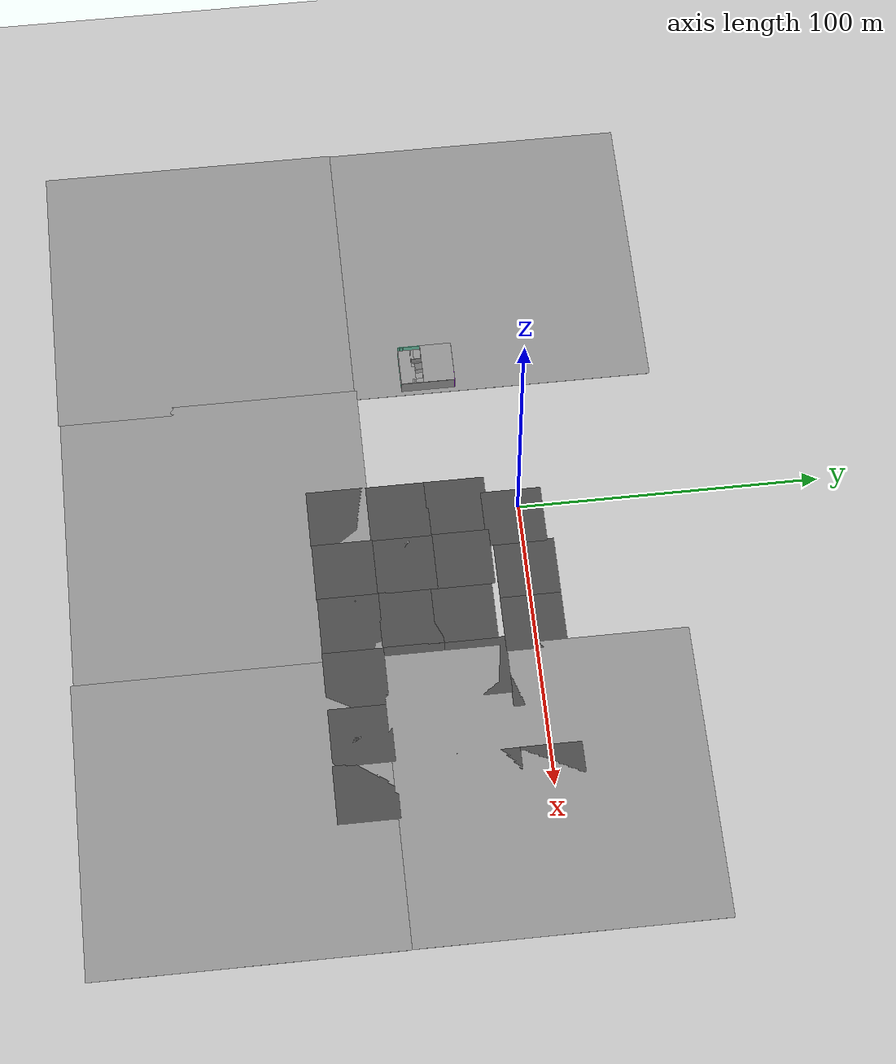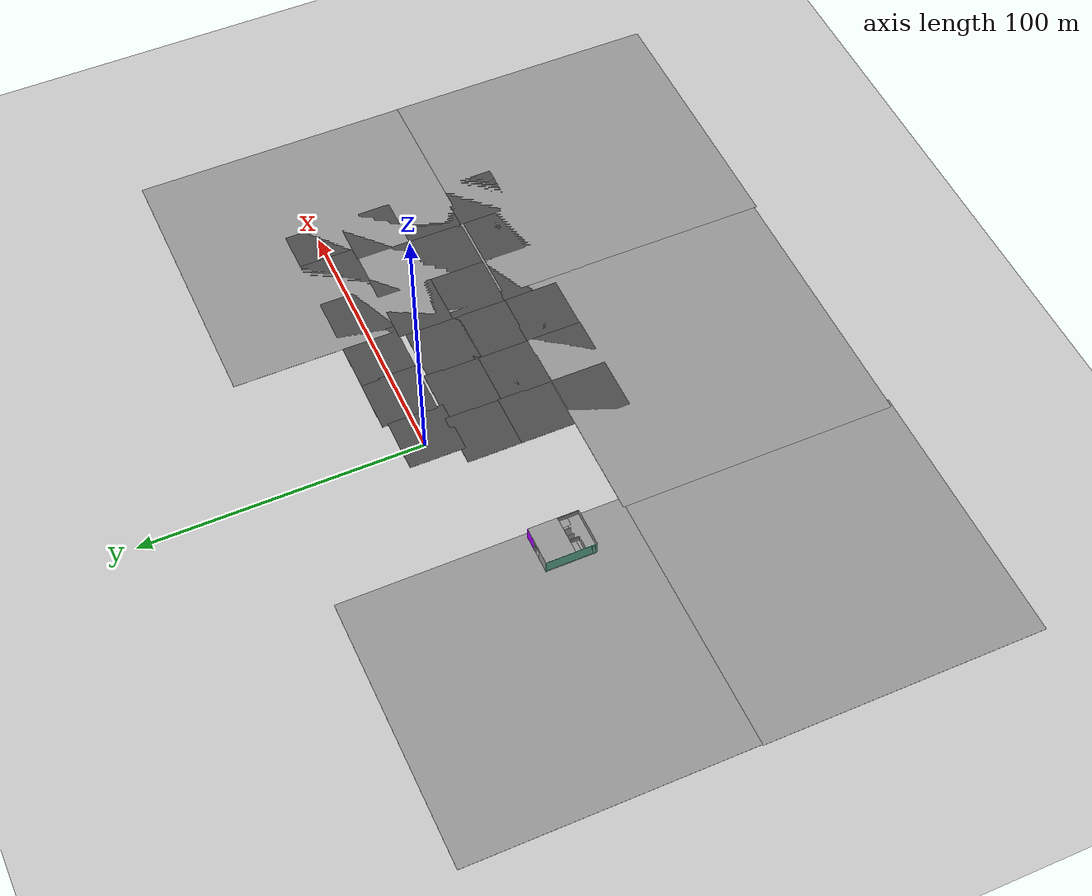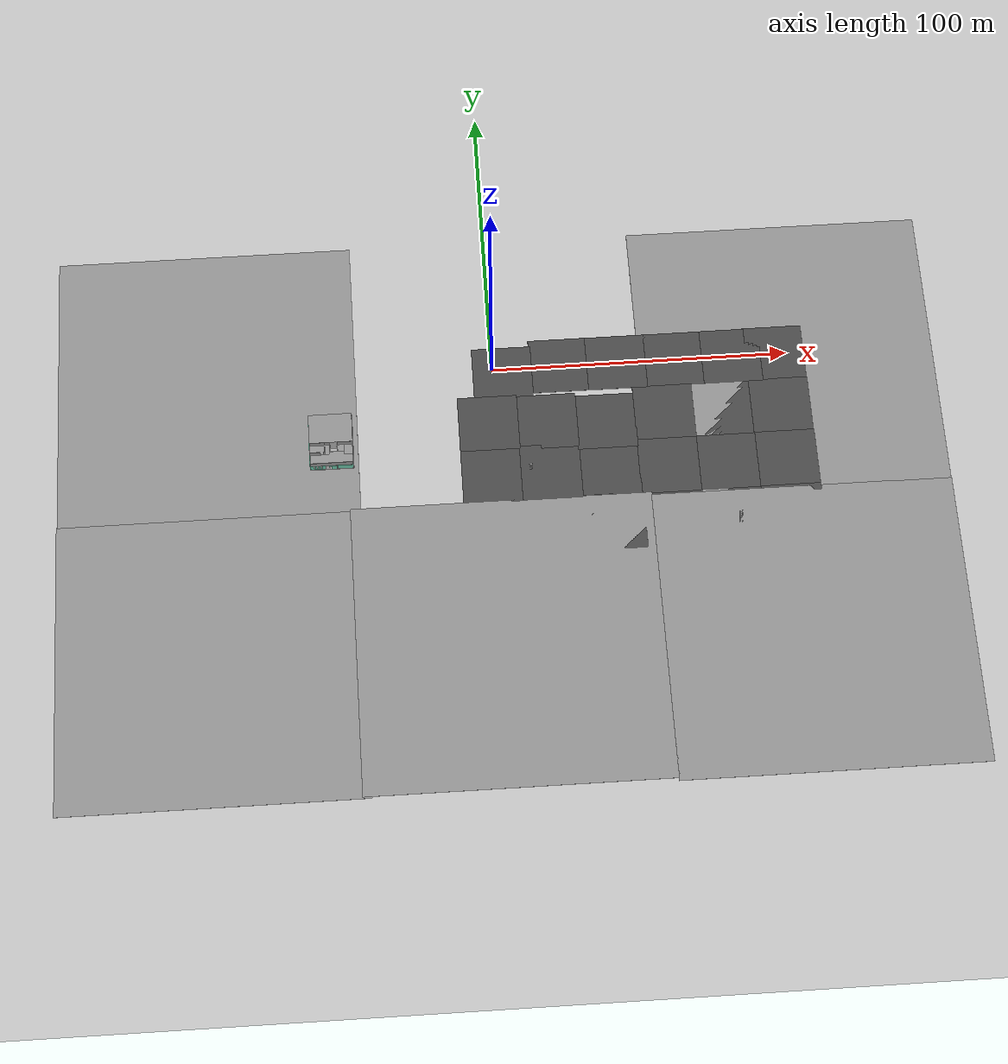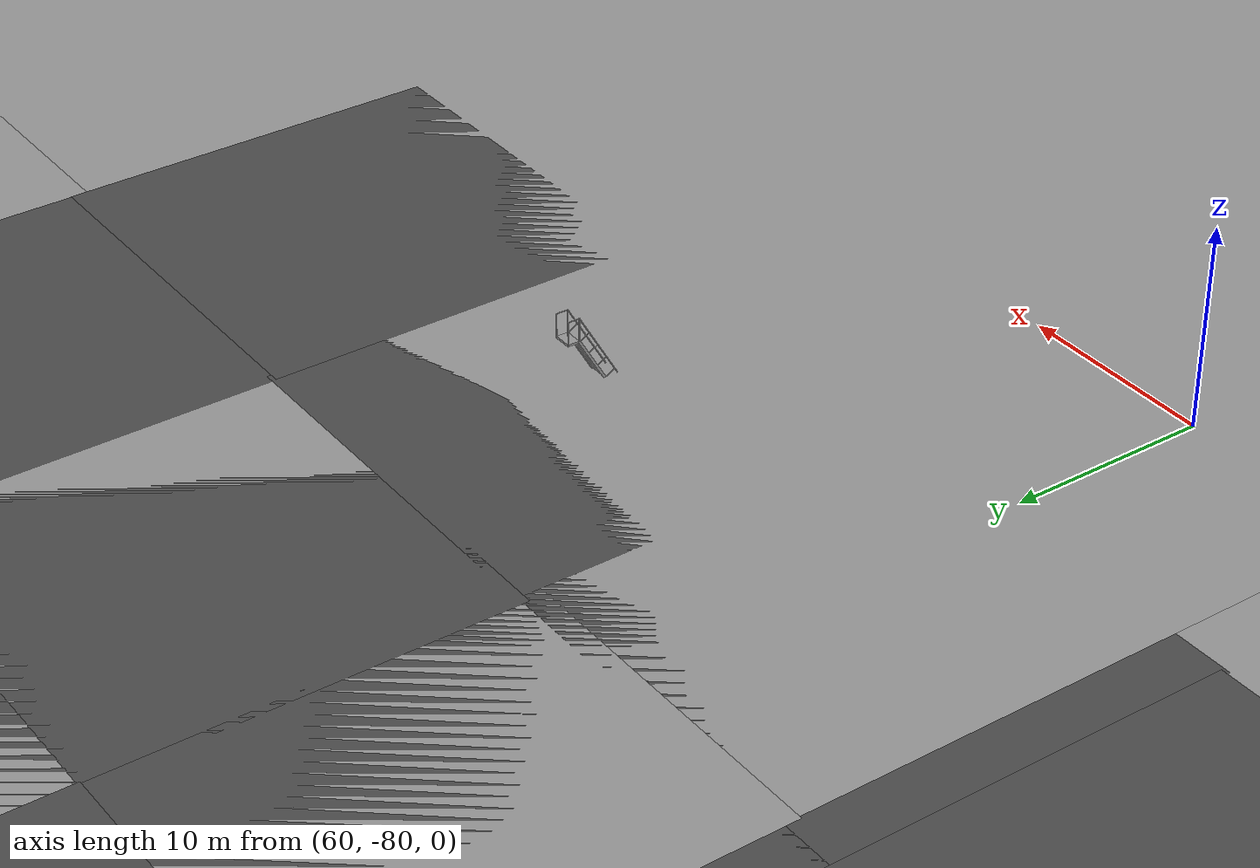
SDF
<sdf version="1.6">
 <world name="default">
  <model name="ground_plane">
   <static>1</static>
   <link name="link">
    <collision name="collision">
     <geometry><plane><normal>0 0 1</normal><size>100 100</size></plane></geometry>
     <surface><friction><ode><mu>100</mu><mu2>50</mu2></ode></friction></surface>
    </collision>
    <visual name="visual">
     <cast_shadows>0</cast_shadows>
     <geometry><plane><normal>0 0 1</normal><size>100 100</size></plane></geometry>
     <material>
      <script><uri>file://media/materials/scripts/gazebo.material</uri><name>Gazebo/Grey</name></script>
     </material>
    </visual>
   </link>
  </model>
  <light name="sun" type="directional">
   <pose>0 0 10 0 -0 0</pose>
   <diffuse>0.8 0.8 0.8 1</diffuse>
   <specular>0.2 0.2 0.2 1</specular>
   <attenuation>
    <range>1000</range>
    <constant>0.9</constant>
    <linear>0.01</linear>
    <quadratic>0.001</quadratic>
   </attenuation>
   <direction>-0.5 0.1 -0.9</direction>
  </light>
  <gravity>0 0 -9.8</gravity>
  <magnetic_field>6e-06 2.3e-05 -4.2e-05</magnetic_field>
  <atmosphere type="adiabatic"/>
  <physics name="default_physics" default="0" type="ode">
   <max_step_size>0.001</max_step_size>
   <real_time_factor>1</real_time_factor>
   <real_time_update_rate>1000</real_time_update_rate>
  </physics>
  <scene><ambient>0.4 0.4 0.4 1</ambient><background>0.7 0.7 0.7 1</background><shadows>1</shadows></scene>
  <spherical_coordinates>
   <surface_model>EARTH_WGS84</surface_model>
   <latitude_deg>0</latitude_deg>
   <longitude_deg>0</longitude_deg>
   <elevation>0</elevation>
   <heading_deg>0</heading_deg>
  </spherical_coordinates>
  <model name="ground_plane_0">
   <static>1</static>
   <link name="link">
    <collision name="collision">
     <geometry><plane><normal>0 0 1</normal><size>100 100</size></plane></geometry>
     <surface><friction><ode><mu>100</mu><mu2>50</mu2></ode></friction></surface>
    </collision>
    <visual name="visual">
     <cast_shadows>0</cast_shadows>
     <geometry><plane><normal>0 0 1</normal><size>100 100</size></plane></geometry>
     <material>
      <script><uri>file://media/materials/scripts/gazebo.material</uri><name>Gazebo/Grey</name></script>
     </material>
    </visual>
   </link>
   <pose>-0.037273 -99.0745 0 0 -0 0</pose>
  </model>
  <model name="ground_plane_1">
   <static>1</static>
   <link name="link">
    <collision name="collision">
     <geometry><plane><normal>0 0 1</normal><size>100 100</size></plane></geometry>
     <surface><friction><ode><mu>100</mu><mu2>50</mu2></ode></friction></surface>
    </collision>
    <visual name="visual">
     <cast_shadows>0</cast_shadows>
     <geometry><plane><normal>0 0 1</normal><size>100 100</size></plane></geometry>
     <material>
      <script><uri>file://media/materials/scripts/gazebo.material</uri><name>Gazebo/Grey</name></script>
     </material>
    </visual>
   </link>
   <pose>99.5974 -0.193372 0 0 -0 0</pose>
  </model>
  <model name="ground_plane_2">
   <static>1</static>
   <link name="link">
    <collision name="collision">
     <geometry><plane><normal>0 0 1</normal><size>100 100</size></plane></geometry>
     <surface><friction><ode><mu>100</mu><mu2>50</mu2></ode></friction></surface>
    </collision>
    <visual name="visual">
     <cast_shadows>0</cast_shadows>
     <geometry><plane><normal>0 0 1</normal><size>100 100</size></plane></geometry>
     <material>
      <script><uri>file://media/materials/scripts/gazebo.material</uri><name>Gazebo/Grey</name></script>
     </material>
    </visual>
   </link>
   <pose>99.7181 -100.033 0 0 -0 0</pose>
  </model>
  <model name="ground_plane_3">
   <static>1</static>
   <link name="link">
    <collision name="collision">
     <geometry><plane><normal>0 0 1</normal><size>100 100</size></plane></geometry>
     <surface><friction><ode><mu>100</mu><mu2>50</mu2></ode></friction></surface>
    </collision>
    <visual name="visual">
     <cast_shadows>0</cast_shadows>
     <geometry><plane><normal>0 0 1</normal><size>100 100</size></plane></geometry>
     <material>
      <script><uri>file://media/materials/scripts/gazebo.material</uri><name>Gazebo/Grey</name></script>
     </material>
    </visual>
   </link>
   <pose>-96.4927 0.207294 0 0 -0 0</pose>
  </model>
  <model name="ground_plane_4">
   <static>1</static>
   <link name="link">
    <collision name="collision">
     <geometry><plane><normal>0 0 1</normal><size>100 100</size></plane></geometry>
     <surface><friction><ode><mu>100</mu><mu2>50</mu2></ode></friction></surface>
    </collision>
    <visual name="visual">
     <cast_shadows>0</cast_shadows>
     <geometry><plane><normal>0 0 1</normal><size>100 100</size></plane></geometry>
     <material>
      <script><uri>file://media/materials/scripts/gazebo.material</uri><name>Gazebo/Grey</name></script>
     </material>
    </visual>
   </link>
   <pose>-96.8227 -99.6308 0 0 -0 0</pose>
  </model>
  <model name="ladder_60deg_2rails">
   <static>1</static>
   <link name="step0">
    <pose>0 0.15396 0.266667 0 -0 0</pose>
    <inertial>
     <mass>9.75482</mass>
     <inertia>
      <ixx>0.00957124</ixx>
      <iyy>0.65963</iyy>
      <izz>0.666842</izz>
      <ixy>0</ixy>
      <ixz>0</ixz>
      <iyz>0</iyz>
     </inertia>
    </inertial>
    <collision name="collision"><geometry><box><size>0.9 0.1016 0.0381</size></box></geometry></collision>
    <visual name="visual">
     <geometry><box><size>0.9 0.1016 0.0381</size></box></geometry>
     <material>
      <script><uri>file://media/materials/scripts/gazebo.material</uri><name>Gazebo/Grey</name></script>
     </material>
    </visual>
   </link>
   <link name="step1">
    <pose>0 0.30792 0.533333 0 -0 0</pose>
    <inertial>
     <mass>9.75482</mass>
     <inertia>
      <ixx>0.00957124</ixx>
      <iyy>0.65963</iyy>
      <izz>0.666842</izz>
      <ixy>0</ixy>
      <ixz>0</ixz>
      <iyz>0</iyz>
     </inertia>
    </inertial>
    <collision name="collision"><geometry><box><size>0.9 0.1016 0.0381</size></box></geometry></collision>
    <visual name="visual">
     <geometry><box><size>0.9 0.1016 0.0381</size></box></geometry>
     <material>
      <script><uri>file://media/materials/scripts/gazebo.material</uri><name>Gazebo/Grey</name></script>
     </material>
    </visual>
   </link>
   <link name="step2">
    <pose>0 0.46188 0.8 0 -0 0</pose>
    <inertial>
     <mass>9.75482</mass>
     <inertia>
      <ixx>0.00957124</ixx>
      <iyy>0.65963</iyy>
      <izz>0.666842</izz>
      <ixy>0</ixy>
      <ixz>0</ixz>
      <iyz>0</iyz>
     </inertia>
    </inertial>
    <collision name="collision"><geometry><box><size>0.9 0.1016 0.0381</size></box></geometry></collision>
    <visual name="visual">
     <geometry><box><size>0.9 0.1016 0.0381</size></box></geometry>
     <material>
      <script><uri>file://media/materials/scripts/gazebo.material</uri><name>Gazebo/Grey</name></script>
     </material>
    </visual>
   </link>
   <link name="step3">
    <pose>0 0.61584 1.06667 0 -0 0</pose>
    <inertial>
     <mass>9.75482</mass>
     <inertia>
      <ixx>0.00957124</ixx>
      <iyy>0.65963</iyy>
      <izz>0.666842</izz>
      <ixy>0</ixy>
      <ixz>0</ixz>
      <iyz>0</iyz>
     </inertia>
    </inertial>
    <collision name="collision"><geometry><box><size>0.9 0.1016 0.0381</size></box></geometry></collision>
    <visual name="visual">
     <geometry><box><size>0.9 0.1016 0.0381</size></box></geometry>
     <material>
      <script><uri>file://media/materials/scripts/gazebo.material</uri><name>Gazebo/Grey</name></script>
     </material>
    </visual>
   </link>
   <link name="step4">
    <pose>0 0.7698 1.33333 0 -0 0</pose>
    <inertial>
     <mass>9.75482</mass>
     <inertia>
      <ixx>0.00957124</ixx>
      <iyy>0.65963</iyy>
      <izz>0.666842</izz>
      <ixy>0</ixy>
      <ixz>0</ixz>
      <iyz>0</iyz>
     </inertia>
    </inertial>
    <collision name="collision"><geometry><box><size>0.9 0.1016 0.0381</size></box></geometry></collision>
    <visual name="visual">
     <geometry><box><size>0.9 0.1016 0.0381</size></box></geometry>
     <material>
      <script><uri>file://media/materials/scripts/gazebo.material</uri><name>Gazebo/Grey</name></script>
     </material>
    </visual>
   </link>
   <link name="step5">
    <pose>0 0.92376 1.6 0 -0 0</pose>
    <inertial>
     <mass>9.75482</mass>
     <inertia>
      <ixx>0.00957124</ixx>
      <iyy>0.65963</iyy>
      <izz>0.666842</izz>
      <ixy>0</ixy>
      <ixz>0</ixz>
      <iyz>0</iyz>
     </inertia>
    </inertial>
    <collision name="collision"><geometry><box><size>0.9 0.1016 0.0381</size></box></geometry></collision>
    <visual name="visual">
     <geometry><box><size>0.9 0.1016 0.0381</size></box></geometry>
     <material>
      <script><uri>file://media/materials/scripts/gazebo.material</uri><name>Gazebo/Grey</name></script>
     </material>
    </visual>
   </link>
   <link name="step6">
    <pose>0 1.07772 1.86667 0 -0 0</pose>
    <inertial>
     <mass>9.75482</mass>
     <inertia>
      <ixx>0.00957124</ixx>
      <iyy>0.65963</iyy>
      <izz>0.666842</izz>
      <ixy>0</ixy>
      <ixz>0</ixz>
      <iyz>0</iyz>
     </inertia>
    </inertial>
    <collision name="collision"><geometry><box><size>0.9 0.1016 0.0381</size></box></geometry></collision>
    <visual name="visual">
     <geometry><box><size>0.9 0.1016 0.0381</size></box></geometry>
     <material>
      <script><uri>file://media/materials/scripts/gazebo.material</uri><name>Gazebo/Grey</name></script>
     </material>
    </visual>
   </link>
   <link name="step7">
    <pose>0 1.23168 2.13333 0 -0 0</pose>
    <inertial>
     <mass>9.75482</mass>
     <inertia>
      <ixx>0.00957124</ixx>
      <iyy>0.65963</iyy>
      <izz>0.666842</izz>
      <ixy>0</ixy>
      <ixz>0</ixz>
      <iyz>0</iyz>
     </inertia>
    </inertial>
    <collision name="collision"><geometry><box><size>0.9 0.1016 0.0381</size></box></geometry></collision>
    <visual name="visual">
     <geometry><box><size>0.9 0.1016 0.0381</size></box></geometry>
     <material>
      <script><uri>file://media/materials/scripts/gazebo.material</uri><name>Gazebo/Grey</name></script>
     </material>
    </visual>
   </link>
   <link name="landing">
    <pose>0 1.68564 2.4 0 -0 0</pose>
    <inertial>
     <mass>57.6072</mass>
     <inertia><ixx>1.73518</ixx><iyy>3.89545</iyy><izz>5.6167</izz><ixy>0</ixy><ixz>0</ixz><iyz>0</iyz></inertia>
    </inertial>
    <collision name="collision"><geometry><box><size>0.9 0.6 0.1016</size></box></geometry></collision>
    <visual name="visual">
     <geometry><box><size>0.9 0.6 0.1016</size></box></geometry>
     <material>
      <script><uri>file://media/materials/scripts/gazebo.material</uri><name>Gazebo/Grey</name></script>
     </material>
    </visual>
   </link>
   <link name="left_side_wall">
    <pose>-0.45 0.69282 1.2 1.0472 -0 0</pose>
    <collision name="collision"><geometry><box><size>0.0508 2.85128 0.13</size></box></geometry></collision>
    <visual name="visual">
     <geometry><box><size>0.0508 2.85128 0.13</size></box></geometry>
     <material>
      <script><uri>file://media/materials/scripts/gazebo.material</uri><name>Gazebo/Grey</name></script>
     </material>
    </visual>
   </link>
   <link name="right_side_wall">
    <pose>0.45 0.69282 1.2 1.0472 -0 0</pose>
    <collision name="collision"><geometry><box><size>0.0508 2.85128 0.13</size></box></geometry></collision>
    <visual name="visual">
     <geometry><box><size>0.0508 2.85128 0.13</size></box></geometry>
     <material>
      <script><uri>file://media/materials/scripts/gazebo.material</uri><name>Gazebo/Grey</name></script>
     </material>
    </visual>
   </link>
   <link name="left_railing_long">
    <pose>-0.45 0.34282 1.80622 -0.523599 0 0</pose>
    <collision name="collision">
     <geometry><cylinder><radius>0.02413</radius><length>4.17128</length></cylinder></geometry>
    </collision>
    <visual name="visual">
     <geometry><cylinder><radius>0.02413</radius><length>4.17128</length></cylinder></geometry>
     <material>
      <script><uri>file://media/materials/scripts/gazebo.material</uri><name>Gazebo/Grey</name></script>
     </material>
    </visual>
   </link>
   <link name="left_railing_upright0">
    <pose>-0.45 -0.274963 0.15875 1.0472 -0 0</pose>
    <collision name="collision">
     <geometry><cylinder><radius>0.02413</radius><length>0.541218</length></cylinder></geometry>
    </collision>
    <visual name="visual">
     <geometry><cylinder><radius>0.02413</radius><length>0.541218</length></cylinder></geometry>
     <material>
      <script><uri>file://media/materials/scripts/gazebo.material</uri><name>Gazebo/Grey</name></script>
     </material>
    </visual>
   </link>
   <link name="left_railing_upright1">
    <pose>-0.45 0.186917 0.95875 1.0472 -0 0</pose>
    <collision name="collision">
     <geometry><cylinder><radius>0.02413</radius><length>0.541218</length></cylinder></geometry>
    </collision>
    <visual name="visual">
     <geometry><cylinder><radius>0.02413</radius><length>0.541218</length></cylinder></geometry>
     <material>
      <script><uri>file://media/materials/scripts/gazebo.material</uri><name>Gazebo/Grey</name></script>
     </material>
    </visual>
   </link>
   <link name="left_railing_upright2">
    <pose>-0.45 0.648797 1.75875 1.0472 -0 0</pose>
    <collision name="collision">
     <geometry><cylinder><radius>0.02413</radius><length>0.541218</length></cylinder></geometry>
    </collision>
    <visual name="visual">
     <geometry><cylinder><radius>0.02413</radius><length>0.541218</length></cylinder></geometry>
     <material>
      <script><uri>file://media/materials/scripts/gazebo.material</uri><name>Gazebo/Grey</name></script>
     </material>
    </visual>
   </link>
   <link name="left_railing_upright3">
    <pose>-0.45 1.11068 2.55875 1.0472 -0 0</pose>
    <collision name="collision">
     <geometry><cylinder><radius>0.02413</radius><length>0.541218</length></cylinder></geometry>
    </collision>
    <visual name="visual">
     <geometry><cylinder><radius>0.02413</radius><length>0.541218</length></cylinder></geometry>
     <material>
      <script><uri>file://media/materials/scripts/gazebo.material</uri><name>Gazebo/Grey</name></script>
     </material>
    </visual>
   </link>
   <link name="left_railing_landing_top">
    <pose>-0.45 1.68564 3.61244 1.5708 -0 0</pose>
    <collision name="collision">
     <geometry><cylinder><radius>0.02413</radius><length>0.64826</length></cylinder></geometry>
    </collision>
    <visual name="visual">
     <geometry><cylinder><radius>0.02413</radius><length>0.64826</length></cylinder></geometry>
     <material>
      <script><uri>file://media/materials/scripts/gazebo.material</uri><name>Gazebo/Grey</name></script>
     </material>
    </visual>
   </link>
   <link name="left_railing_landing_upright_0">
    <pose>-0.45 1.38564 3.00622 0 -0 0</pose>
    <collision name="collision">
     <geometry><cylinder><radius>0.02413</radius><length>1.21244</length></cylinder></geometry>
    </collision>
    <visual name="visual">
     <geometry><cylinder><radius>0.02413</radius><length>1.21244</length></cylinder></geometry>
     <material>
      <script><uri>file://media/materials/scripts/gazebo.material</uri><name>Gazebo/Grey</name></script>
     </material>
    </visual>
   </link>
   <link name="left_railing_landing_upright_1">
    <pose>-0.45 1.98564 3.00622 0 -0 0</pose>
    <collision name="collision">
     <geometry><cylinder><radius>0.02413</radius><length>1.21244</length></cylinder></geometry>
    </collision>
    <visual name="visual">
     <geometry><cylinder><radius>0.02413</radius><length>1.21244</length></cylinder></geometry>
     <material>
      <script><uri>file://media/materials/scripts/gazebo.material</uri><name>Gazebo/Grey</name></script>
     </material>
    </visual>
   </link>
   <link name="right_railing_long">
    <pose>0.45 0.34282 1.80622 -0.523599 0 0</pose>
    <collision name="collision">
     <geometry><cylinder><radius>0.02413</radius><length>4.17128</length></cylinder></geometry>
    </collision>
    <visual name="visual">
     <geometry><cylinder><radius>0.02413</radius><length>4.17128</length></cylinder></geometry>
     <material>
      <script><uri>file://media/materials/scripts/gazebo.material</uri><name>Gazebo/Grey</name></script>
     </material>
    </visual>
   </link>
   <link name="right_railing_upright0">
    <pose>0.45 -0.274963 0.15875 1.0472 -0 0</pose>
    <collision name="collision">
     <geometry><cylinder><radius>0.02413</radius><length>0.541218</length></cylinder></geometry>
    </collision>
    <visual name="visual">
     <geometry><cylinder><radius>0.02413</radius><length>0.541218</length></cylinder></geometry>
     <material>
      <script><uri>file://media/materials/scripts/gazebo.material</uri><name>Gazebo/Grey</name></script>
     </material>
    </visual>
   </link>
   <link name="right_railing_upright1">
    <pose>0.45 0.186917 0.95875 1.0472 -0 0</pose>
    <collision name="collision">
     <geometry><cylinder><radius>0.02413</radius><length>0.541218</length></cylinder></geometry>
    </collision>
    <visual name="visual">
     <geometry><cylinder><radius>0.02413</radius><length>0.541218</length></cylinder></geometry>
     <material>
      <script><uri>file://media/materials/scripts/gazebo.material</uri><name>Gazebo/Grey</name></script>
     </material>
    </visual>
   </link>
   <link name="right_railing_upright2">
    <pose>0.45 0.648797 1.75875 1.0472 -0 0</pose>
    <collision name="collision">
     <geometry><cylinder><radius>0.02413</radius><length>0.541218</length></cylinder></geometry>
    </collision>
    <visual name="visual">
     <geometry><cylinder><radius>0.02413</radius><length>0.541218</length></cylinder></geometry>
     <material>
      <script><uri>file://media/materials/scripts/gazebo.material</uri><name>Gazebo/Grey</name></script>
     </material>
    </visual>
   </link>
   <link name="right_railing_upright3">
    <pose>0.45 1.11068 2.55875 1.0472 -0 0</pose>
    <collision name="collision">
     <geometry><cylinder><radius>0.02413</radius><length>0.541218</length></cylinder></geometry>
    </collision>
    <visual name="visual">
     <geometry><cylinder><radius>0.02413</radius><length>0.541218</length></cylinder></geometry>
     <material>
      <script><uri>file://media/materials/scripts/gazebo.material</uri><name>Gazebo/Grey</name></script>
     </material>
    </visual>
   </link>
   <link name="right_railing_landing_top">
    <pose>0.45 1.68564 3.61244 1.5708 -0 0</pose>
    <collision name="collision">
     <geometry><cylinder><radius>0.02413</radius><length>0.64826</length></cylinder></geometry>
    </collision>
    <visual name="visual">
     <geometry><cylinder><radius>0.02413</radius><length>0.64826</length></cylinder></geometry>
     <material>
      <script><uri>file://media/materials/scripts/gazebo.material</uri><name>Gazebo/Grey</name></script>
     </material>
    </visual>
   </link>
   <link name="right_railing_landing_upright_0">
    <pose>0.45 1.38564 3.00622 0 -0 0</pose>
    <collision name="collision">
     <geometry><cylinder><radius>0.02413</radius><length>1.21244</length></cylinder></geometry>
    </collision>
    <visual name="visual">
     <geometry><cylinder><radius>0.02413</radius><length>1.21244</length></cylinder></geometry>
     <material>
      <script><uri>file://media/materials/scripts/gazebo.material</uri><name>Gazebo/Grey</name></script>
     </material>
    </visual>
   </link>
   <link name="right_railing_landing_upright_1">
    <pose>0.45 1.98564 3.00622 0 -0 0</pose>
    <collision name="collision">
     <geometry><cylinder><radius>0.02413</radius><length>1.21244</length></cylinder></geometry>
    </collision>
    <visual name="visual">
     <geometry><cylinder><radius>0.02413</radius><length>1.21244</length></cylinder></geometry>
     <material>
      <script><uri>file://media/materials/scripts/gazebo.material</uri><name>Gazebo/Grey</name></script>
     </material>
    </visual>
   </link>
   <pose>78.3894 -61.2924 0 0 -0 0</pose>
  </model>
  <model name="ladder_70deg_0rails">
   <static>1</static>
   <link name="step0">
    <pose>0 0.097059 0.266667 0 -0 0</pose>
    <inertial>
     <mass>9.75482</mass>
     <inertia>
      <ixx>0.00957124</ixx>
      <iyy>0.65963</iyy>
      <izz>0.666842</izz>
      <ixy>0</ixy>
      <ixz>0</ixz>
      <iyz>0</iyz>
     </inertia>
    </inertial>
    <collision name="collision"><geometry><box><size>0.9 0.1016 0.0381</size></box></geometry></collision>
    <visual name="visual">
     <geometry><box><size>0.9 0.1016 0.0381</size></box></geometry>
     <material>
      <script><uri>file://media/materials/scripts/gazebo.material</uri><name>Gazebo/Grey</name></script>
     </material>
    </visual>
   </link>
   <link name="step1">
    <pose>0 0.194117 0.533333 0 -0 0</pose>
    <inertial>
     <mass>9.75482</mass>
     <inertia>
      <ixx>0.00957124</ixx>
      <iyy>0.65963</iyy>
      <izz>0.666842</izz>
      <ixy>0</ixy>
      <ixz>0</ixz>
      <iyz>0</iyz>
     </inertia>
    </inertial>
    <collision name="collision"><geometry><box><size>0.9 0.1016 0.0381</size></box></geometry></collision>
    <visual name="visual">
     <geometry><box><size>0.9 0.1016 0.0381</size></box></geometry>
     <material>
      <script><uri>file://media/materials/scripts/gazebo.material</uri><name>Gazebo/Grey</name></script>
     </material>
    </visual>
   </link>
   <link name="step2">
    <pose>0 0.291176 0.8 0 -0 0</pose>
    <inertial>
     <mass>9.75482</mass>
     <inertia>
      <ixx>0.00957124</ixx>
      <iyy>0.65963</iyy>
      <izz>0.666842</izz>
      <ixy>0</ixy>
      <ixz>0</ixz>
      <iyz>0</iyz>
     </inertia>
    </inertial>
    <collision name="collision"><geometry><box><size>0.9 0.1016 0.0381</size></box></geometry></collision>
    <visual name="visual">
     <geometry><box><size>0.9 0.1016 0.0381</size></box></geometry>
     <material>
      <script><uri>file://media/materials/scripts/gazebo.material</uri><name>Gazebo/Grey</name></script>
     </material>
    </visual>
   </link>
   <link name="step3">
    <pose>0 0.388235 1.06667 0 -0 0</pose>
    <inertial>
     <mass>9.75482</mass>
     <inertia>
      <ixx>0.00957124</ixx>
      <iyy>0.65963</iyy>
      <izz>0.666842</izz>
      <ixy>0</ixy>
      <ixz>0</ixz>
      <iyz>0</iyz>
     </inertia>
    </inertial>
    <collision name="collision"><geometry><box><size>0.9 0.1016 0.0381</size></box></geometry></collision>
    <visual name="visual">
     <geometry><box><size>0.9 0.1016 0.0381</size></box></geometry>
     <material>
      <script><uri>file://media/materials/scripts/gazebo.material</uri><name>Gazebo/Grey</name></script>
     </material>
    </visual>
   </link>
   <link name="step4">
    <pose>0 0.485294 1.33333 0 -0 0</pose>
    <inertial>
     <mass>9.75482</mass>
     <inertia>
      <ixx>0.00957124</ixx>
      <iyy>0.65963</iyy>
      <izz>0.666842</izz>
      <ixy>0</ixy>
      <ixz>0</ixz>
      <iyz>0</iyz>
     </inertia>
    </inertial>
    <collision name="collision"><geometry><box><size>0.9 0.1016 0.0381</size></box></geometry></collision>
    <visual name="visual">
     <geometry><box><size>0.9 0.1016 0.0381</size></box></geometry>
     <material>
      <script><uri>file://media/materials/scripts/gazebo.material</uri><name>Gazebo/Grey</name></script>
     </material>
    </visual>
   </link>
   <link name="step5">
    <pose>0 0.582352 1.6 0 -0 0</pose>
    <inertial>
     <mass>9.75482</mass>
     <inertia>
      <ixx>0.00957124</ixx>
      <iyy>0.65963</iyy>
      <izz>0.666842</izz>
      <ixy>0</ixy>
      <ixz>0</ixz>
      <iyz>0</iyz>
     </inertia>
    </inertial>
    <collision name="collision"><geometry><box><size>0.9 0.1016 0.0381</size></box></geometry></collision>
    <visual name="visual">
     <geometry><box><size>0.9 0.1016 0.0381</size></box></geometry>
     <material>
      <script><uri>file://media/materials/scripts/gazebo.material</uri><name>Gazebo/Grey</name></script>
     </material>
    </visual>
   </link>
   <link name="step6">
    <pose>0 0.679411 1.86667 0 -0 0</pose>
    <inertial>
     <mass>9.75482</mass>
     <inertia>
      <ixx>0.00957124</ixx>
      <iyy>0.65963</iyy>
      <izz>0.666842</izz>
      <ixy>0</ixy>
      <ixz>0</ixz>
      <iyz>0</iyz>
     </inertia>
    </inertial>
    <collision name="collision"><geometry><box><size>0.9 0.1016 0.0381</size></box></geometry></collision>
    <visual name="visual">
     <geometry><box><size>0.9 0.1016 0.0381</size></box></geometry>
     <material>
      <script><uri>file://media/materials/scripts/gazebo.material</uri><name>Gazebo/Grey</name></script>
     </material>
    </visual>
   </link>
   <link name="step7">
    <pose>0 0.77647 2.13333 0 -0 0</pose>
    <inertial>
     <mass>9.75482</mass>
     <inertia>
      <ixx>0.00957124</ixx>
      <iyy>0.65963</iyy>
      <izz>0.666842</izz>
      <ixy>0</ixy>
      <ixz>0</ixz>
      <iyz>0</iyz>
     </inertia>
    </inertial>
    <collision name="collision"><geometry><box><size>0.9 0.1016 0.0381</size></box></geometry></collision>
    <visual name="visual">
     <geometry><box><size>0.9 0.1016 0.0381</size></box></geometry>
     <material>
      <script><uri>file://media/materials/scripts/gazebo.material</uri><name>Gazebo/Grey</name></script>
     </material>
    </visual>
   </link>
   <link name="landing">
    <pose>0 1.17353 2.4 0 -0 0</pose>
    <inertial>
     <mass>57.6072</mass>
     <inertia><ixx>1.73518</ixx><iyy>3.89545</iyy><izz>5.6167</izz><ixy>0</ixy><ixz>0</ixz><iyz>0</iyz></inertia>
    </inertial>
    <collision name="collision"><geometry><box><size>0.9 0.6 0.1016</size></box></geometry></collision>
    <visual name="visual">
     <geometry><box><size>0.9 0.6 0.1016</size></box></geometry>
     <material>
      <script><uri>file://media/materials/scripts/gazebo.material</uri><name>Gazebo/Grey</name></script>
     </material>
    </visual>
   </link>
   <link name="left_side_wall">
    <pose>-0.45 0.436764 1.2 1.22173 -0 0</pose>
    <collision name="collision"><geometry><box><size>0.0508 2.63403 0.13</size></box></geometry></collision>
    <visual name="visual">
     <geometry><box><size>0.0508 2.63403 0.13</size></box></geometry>
     <material>
      <script><uri>file://media/materials/scripts/gazebo.material</uri><name>Gazebo/Grey</name></script>
     </material>
    </visual>
   </link>
   <link name="right_side_wall">
    <pose>0.45 0.436764 1.2 1.22173 -0 0</pose>
    <collision name="collision"><geometry><box><size>0.0508 2.63403 0.13</size></box></geometry></collision>
    <visual name="visual">
     <geometry><box><size>0.0508 2.63403 0.13</size></box></geometry>
     <material>
      <script><uri>file://media/materials/scripts/gazebo.material</uri><name>Gazebo/Grey</name></script>
     </material>
    </visual>
   </link>
   <pose>10.5177 -38.6481 0 0 -0 0</pose>
  </model>
  <model name="osrf_elevator">
   <link name="Wall_0">
    <pose>-7.17647 0.013004 0 0 -0 1.57174</pose>
    <visual name="Wall_0_Visual_0">
     <meta><layer>0</layer></meta>
     <pose>-8.72596 0 2.4385 0 -0 0</pose>
     <geometry><box><size>0.663656 0.15 4.877</size></box></geometry>
     <material>
      <script><uri>file://media/materials/scripts/gazebo.material</uri><name>Gazebo/Grey</name></script>
      <ambient>0.435294 0.796078 0.67451 1</ambient>
     </material>
    </visual>
    <collision name="Wall_0_Collision_0">
     <geometry><box><size>0.663656 0.15 4.877</size></box></geometry>
     <pose>-8.72596 0 2.4385 0 -0 0</pose>
    </collision>
    <visual name="Wall_0_Visual_1">
     <meta><layer>0</layer></meta>
     <pose>0.331828 0 0.25 0 -0 0</pose>
     <geometry><box><size>17.4519 0.15 0.5</size></box></geometry>
     <material>
      <script><uri>file://media/materials/scripts/gazebo.material</uri><name>Gazebo/Grey</name></script>
      <ambient>0.435294 0.796078 0.67451 1</ambient>
     </material>
    </visual>
    <collision name="Wall_0_Collision_1">
     <geometry><box><size>17.4519 0.15 0.5</size></box></geometry>
     <pose>0.331828 0 0.25 0 -0 0</pose>
    </collision>
    <visual name="Wall_0_Visual_2">
     <meta><layer>0</layer></meta>
     <pose>-7.67281 0 2.6885 0 -0 0</pose>
     <geometry><box><size>0.816657 0.15 4.377</size></box></geometry>
     <material>
      <script><uri>file://media/materials/scripts/gazebo.material</uri><name>Gazebo/Grey</name></script>
      <ambient>0.435294 0.796078 0.67451 1</ambient>
     </material>
    </visual>
    <collision name="Wall_0_Collision_2">
     <geometry><box><size>0.816657 0.15 4.377</size></box></geometry>
     <pose>-7.67281 0 2.6885 0 -0 0</pose>
    </collision>
    <visual name="Wall_0_Visual_3">
     <meta><layer>0</layer></meta>
     <pose>1.05709 0 2.6885 0 -0 0</pose>
     <geometry><box><size>16.0014 0.15 4.377</size></box></geometry>
     <material>
      <script><uri>file://media/materials/scripts/gazebo.material</uri><name>Gazebo/Grey</name></script>
      <ambient>0.435294 0.796078 0.67451 1</ambient>
     </material>
    </visual>
    <collision name="Wall_0_Collision_3">
     <geometry><box><size>16.0014 0.15 4.377</size></box></geometry>
     <pose>1.05709 0 2.6885 0 -0 0</pose>
    </collision>
    <visual name="Wall_0_Visual_4">
     <meta><layer>0</layer></meta>
     <pose>-8.23763 0 3.6885 0 -0 0</pose>
     <geometry><box><size>0.313 0.15 2.377</size></box></geometry>
     <material>
      <script><uri>file://media/materials/scripts/gazebo.material</uri><name>Gazebo/Grey</name></script>
      <ambient>0.435294 0.796078 0.67451 1</ambient>
     </material>
    </visual>
    <collision name="Wall_0_Collision_4">
     <geometry><box><size>0.313 0.15 2.377</size></box></geometry>
     <pose>-8.23763 0 3.6885 0 -0 0</pose>
    </collision>
    <visual name="Wall_0_Visual_5">
     <meta><layer>0</layer></meta>
     <pose>-7.10405 0 3.6885 0 -0 0</pose>
     <geometry><box><size>0.320861 0.15 2.377</size></box></geometry>
     <material>
      <script><uri>file://media/materials/scripts/gazebo.material</uri><name>Gazebo/Grey</name></script>
      <ambient>0.435294 0.796078 0.67451 1</ambient>
     </material>
    </visual>
    <collision name="Wall_0_Collision_5">
     <geometry><box><size>0.320861 0.15 2.377</size></box></geometry>
     <pose>-7.10405 0 3.6885 0 -0 0</pose>
    </collision>
   </link>
   <link name="Wall_10">
    <pose>3.11003 -4.9485 0 0 -0 0</pose>
    <visual name="Wall_10_Visual_0">
     <meta><layer>0</layer></meta>
     <pose>-1.73626 0 1.3715 0 -0 0</pose>
     <geometry><box><size>4.52747 0.15 2.743</size></box></geometry>
     <material>
      <script><uri>file://media/materials/scripts/gazebo.material</uri><name>Gazebo/Grey</name></script>
      <ambient>0 0.666667 0 1</ambient>
     </material>
    </visual>
    <collision name="Wall_10_Collision_0">
     <geometry><box><size>4.52747 0.15 2.743</size></box></geometry>
     <pose>-1.73626 0 1.3715 0 -0 0</pose>
    </collision>
    <visual name="Wall_10_Visual_1">
     <meta><layer>0</layer></meta>
     <pose>2.58694 0 1.3715 0 -0 0</pose>
     <geometry><box><size>2.82611 0.15 2.743</size></box></geometry>
     <material>
      <script><uri>file://media/materials/scripts/gazebo.material</uri><name>Gazebo/Grey</name></script>
      <ambient>0 0.666667 0 1</ambient>
     </material>
    </visual>
    <collision name="Wall_10_Collision_1">
     <geometry><box><size>2.82611 0.15 2.743</size></box></geometry>
     <pose>2.58694 0 1.3715 0 -0 0</pose>
    </collision>
    <visual name="Wall_10_Visual_2">
     <meta><layer>0</layer></meta>
     <pose>0.85068 0 2.3715 0 -0 0</pose>
     <geometry><box><size>0.646413 0.15 0.743</size></box></geometry>
     <material>
      <script><uri>file://media/materials/scripts/gazebo.material</uri><name>Gazebo/Grey</name></script>
      <ambient>0 0.666667 0 1</ambient>
     </material>
    </visual>
    <collision name="Wall_10_Collision_2">
     <geometry><box><size>0.646413 0.15 0.743</size></box></geometry>
     <pose>0.85068 0 2.3715 0 -0 0</pose>
    </collision>
   </link>
   <link name="Wall_14">
    <pose>1.83803 -6.9775 0 0 -0 1.5708</pose>
    <visual name="Wall_14_Visual_0">
     <meta><layer>0</layer></meta>
     <pose>-0.387674 0 1.3715 0 -0 0</pose>
     <geometry><box><size>3.41138 0.15 2.743</size></box></geometry>
     <material>
      <script><uri>file://media/materials/scripts/gazebo.material</uri><name>Gazebo/Grey</name></script>
      <ambient>1 1 1 1</ambient>
     </material>
    </visual>
    <collision name="Wall_14_Collision_0">
     <geometry><box><size>3.41138 0.15 2.743</size></box></geometry>
     <pose>-0.387674 0 1.3715 0 -0 0</pose>
    </collision>
    <visual name="Wall_14_Visual_1">
     <meta><layer>0</layer></meta>
     <pose>2.00133 0 1.3715 0 -0 0</pose>
     <geometry><box><size>0.184063 0.15 2.743</size></box></geometry>
     <material>
      <script><uri>file://media/materials/scripts/gazebo.material</uri><name>Gazebo/Grey</name></script>
      <ambient>1 1 1 1</ambient>
     </material>
    </visual>
    <collision name="Wall_14_Collision_1">
     <geometry><box><size>0.184063 0.15 2.743</size></box></geometry>
     <pose>2.00133 0 1.3715 0 -0 0</pose>
    </collision>
    <visual name="Wall_14_Visual_2">
     <meta><layer>0</layer></meta>
     <pose>1.61366 0 2.3715 0 -0 0</pose>
     <geometry><box><size>0.591285 0.15 0.743</size></box></geometry>
     <material>
      <script><uri>file://media/materials/scripts/gazebo.material</uri><name>Gazebo/Grey</name></script>
      <ambient>1 1 1 1</ambient>
     </material>
    </visual>
    <collision name="Wall_14_Collision_2">
     <geometry><box><size>0.591285 0.15 0.743</size></box></geometry>
     <pose>1.61366 0 2.3715 0 -0 0</pose>
    </collision>
   </link>
   <link name="Wall_16">
    <collision name="Wall_16_Collision">
     <geometry><box><size>5.12727 0.15 2.743</size></box></geometry>
     <pose>0 0 1.3715 0 -0 0</pose>
    </collision>
    <visual name="Wall_16_Visual">
     <meta><layer>0</layer></meta>
     <pose>0 0 1.3715 0 -0 0</pose>
     <geometry><box><size>5.12727 0.15 2.743</size></box></geometry>
     <material>
      <script><uri>file://media/materials/scripts/gazebo.material</uri><name>Gazebo/Grey</name></script>
      <ambient>1 1 1 1</ambient>
     </material>
    </visual>
    <pose>-4.68247 -1.4425 0 0 -0 0</pose>
   </link>
   <link name="Wall_17">
    <pose>-2.19097 -3.185 0 0 0 -1.56907</pose>
    <visual name="Wall_17_Visual_0">
     <meta><layer>0</layer></meta>
     <pose>-1.22855 0 1.3715 0 -0 0</pose>
     <geometry><box><size>1.17851 0.15 2.743</size></box></geometry>
     <material>
      <script><uri>file://media/materials/scripts/gazebo.material</uri><name>Gazebo/Grey</name></script>
      <ambient>1 1 1 1</ambient>
     </material>
    </visual>
    <collision name="Wall_17_Collision_0">
     <geometry><box><size>1.17851 0.15 2.743</size></box></geometry>
     <pose>-1.22855 0 1.3715 0 -0 0</pose>
    </collision>
    <visual name="Wall_17_Visual_1">
     <meta><layer>0</layer></meta>
     <pose>0.886237 0 1.3715 0 -0 0</pose>
     <geometry><box><size>1.86314 0.15 2.743</size></box></geometry>
     <material>
      <script><uri>file://media/materials/scripts/gazebo.material</uri><name>Gazebo/Grey</name></script>
      <ambient>1 1 1 1</ambient>
     </material>
    </visual>
    <collision name="Wall_17_Collision_1">
     <geometry><box><size>1.86314 0.15 2.743</size></box></geometry>
     <pose>0.886237 0 1.3715 0 -0 0</pose>
    </collision>
    <visual name="Wall_17_Visual_2">
     <meta><layer>0</layer></meta>
     <pose>1.18873 0 1.3715 0 -0 0</pose>
     <geometry><box><size>1.25815 0.15 2.743</size></box></geometry>
     <material>
      <script><uri>file://media/materials/scripts/gazebo.material</uri><name>Gazebo/Grey</name></script>
      <ambient>1 1 1 1</ambient>
     </material>
    </visual>
    <collision name="Wall_17_Collision_2">
     <geometry><box><size>1.25815 0.15 2.743</size></box></geometry>
     <pose>1.18873 0 1.3715 0 -0 0</pose>
    </collision>
    <visual name="Wall_17_Visual_3">
     <meta><layer>0</layer></meta>
     <pose>-0.345304 0 2.3715 0 -0 0</pose>
     <geometry><box><size>0.587991 0.15 0.743</size></box></geometry>
     <material>
      <script><uri>file://media/materials/scripts/gazebo.material</uri><name>Gazebo/Grey</name></script>
      <ambient>1 1 1 1</ambient>
     </material>
    </visual>
    <collision name="Wall_17_Collision_3">
     <geometry><box><size>0.587991 0.15 0.743</size></box></geometry>
     <pose>-0.345304 0 2.3715 0 -0 0</pose>
    </collision>
   </link>
   <link name="Wall_18">
    <collision name="Wall_18_Collision">
     <geometry><box><size>5 0.15 2.743</size></box></geometry>
     <pose>0 0 1.3715 0 -0 0</pose>
    </collision>
    <visual name="Wall_18_Visual">
     <meta><layer>0</layer></meta>
     <pose>0 0 1.3715 0 -0 0</pose>
     <geometry><box><size>5 0.15 2.743</size></box></geometry>
     <material>
      <script><uri>file://media/materials/scripts/gazebo.material</uri><name>Gazebo/Grey</name></script>
      <ambient>1 1 1 1</ambient>
     </material>
    </visual>
    <pose>-4.61297 -4.9275 0 0 -0 3.14159</pose>
   </link>
   <link name="Wall_20">
    <collision name="Wall_20_Collision">
     <geometry><box><size>2.88731 0.15 2.743</size></box></geometry>
     <pose>0 0 1.3715 0 -0 0</pose>
    </collision>
    <visual name="Wall_20_Visual">
     <meta><layer>0</layer></meta>
     <pose>0 0 1.3715 0 -0 0</pose>
     <geometry><box><size>2.88731 0.15 2.743</size></box></geometry>
     <material>
      <script><uri>file://media/materials/scripts/gazebo.material</uri><name>Gazebo/Grey</name></script>
      <ambient>1 1 1 1</ambient>
     </material>
    </visual>
    <pose>5.74253 1.037 0 0 0 -3.1383</pose>
   </link>
   <link name="Wall_21">
    <pose>4.37403 -1.8925 0 0 0 -1.5708</pose>
    <visual name="Wall_21_Visual_0">
     <meta><layer>0</layer></meta>
     <pose>-2.34405 0 1.3715 0 -0 0</pose>
     <geometry><box><size>1.3119 0.15 2.743</size></box></geometry>
     <material>
      <script><uri>file://media/materials/scripts/gazebo.material</uri><name>Gazebo/Grey</name></script>
      <ambient>1 1 1 1</ambient>
     </material>
    </visual>
    <collision name="Wall_21_Collision_0">
     <geometry><box><size>1.3119 0.15 2.743</size></box></geometry>
     <pose>-2.34405 0 1.3715 0 -0 0</pose>
    </collision>
    <visual name="Wall_21_Visual_1">
     <meta><layer>0</layer></meta>
     <pose>-0.970323 0 1.3715 0 -0 0</pose>
     <geometry><box><size>0.213619 0.15 2.743</size></box></geometry>
     <material>
      <script><uri>file://media/materials/scripts/gazebo.material</uri><name>Gazebo/Grey</name></script>
      <ambient>1 1 1 1</ambient>
     </material>
    </visual>
    <collision name="Wall_21_Collision_1">
     <geometry><box><size>0.213619 0.15 2.743</size></box></geometry>
     <pose>-0.970323 0 1.3715 0 -0 0</pose>
    </collision>
    <visual name="Wall_21_Visual_2">
     <meta><layer>0</layer></meta>
     <pose>0.938748 0 1.3715 0 -0 0</pose>
     <geometry><box><size>2.36558 0.15 2.743</size></box></geometry>
     <material>
      <script><uri>file://media/materials/scripts/gazebo.material</uri><name>Gazebo/Grey</name></script>
      <ambient>1 1 1 1</ambient>
     </material>
    </visual>
    <collision name="Wall_21_Collision_2">
     <geometry><box><size>2.36558 0.15 2.743</size></box></geometry>
     <pose>0.938748 0 1.3715 0 -0 0</pose>
    </collision>
    <visual name="Wall_21_Visual_3">
     <meta><layer>0</layer></meta>
     <pose>2.89346 0 1.3715 0 -0 0</pose>
     <geometry><box><size>0.213086 0.15 2.743</size></box></geometry>
     <material>
      <script><uri>file://media/materials/scripts/gazebo.material</uri><name>Gazebo/Grey</name></script>
      <ambient>1 1 1 1</ambient>
     </material>
    </visual>
    <collision name="Wall_21_Collision_3">
     <geometry><box><size>0.213086 0.15 2.743</size></box></geometry>
     <pose>2.89346 0 1.3715 0 -0 0</pose>
    </collision>
    <visual name="Wall_21_Visual_4">
     <meta><layer>0</layer></meta>
     <pose>-1.38262 0 2.3715 0 -0 0</pose>
     <geometry><box><size>0.610969 0.15 0.743</size></box></geometry>
     <material>
      <script><uri>file://media/materials/scripts/gazebo.material</uri><name>Gazebo/Grey</name></script>
      <ambient>1 1 1 1</ambient>
     </material>
    </visual>
    <collision name="Wall_21_Collision_4">
     <geometry><box><size>0.610969 0.15 0.743</size></box></geometry>
     <pose>-1.38262 0 2.3715 0 -0 0</pose>
    </collision>
    <visual name="Wall_21_Visual_5">
     <meta><layer>0</layer></meta>
     <pose>-0.553779 0 2.3715 0 -0 0</pose>
     <geometry><box><size>0.61947 0.15 0.743</size></box></geometry>
     <material>
      <script><uri>file://media/materials/scripts/gazebo.material</uri><name>Gazebo/Grey</name></script>
      <ambient>1 1 1 1</ambient>
     </material>
    </visual>
    <collision name="Wall_21_Collision_5">
     <geometry><box><size>0.61947 0.15 0.743</size></box></geometry>
     <pose>-0.553779 0 2.3715 0 -0 0</pose>
    </collision>
    <visual name="Wall_21_Visual_6">
     <meta><layer>0</layer></meta>
     <pose>2.45423 0 2.3715 0 -0 0</pose>
     <geometry><box><size>0.665375 0.15 0.743</size></box></geometry>
     <material>
      <script><uri>file://media/materials/scripts/gazebo.material</uri><name>Gazebo/Grey</name></script>
      <ambient>1 1 1 1</ambient>
     </material>
    </visual>
    <collision name="Wall_21_Collision_6">
     <geometry><box><size>0.665375 0.15 0.743</size></box></geometry>
     <pose>2.45423 0 2.3715 0 -0 0</pose>
    </collision>
   </link>
   <link name="Wall_23">
    <collision name="Wall_23_Collision">
     <geometry><box><size>2.75 0.15 2.743</size></box></geometry>
     <pose>0 0 1.3715 0 -0 0</pose>
    </collision>
    <visual name="Wall_23_Visual">
     <meta><layer>0</layer></meta>
     <pose>0 0 1.3715 0 -0 0</pose>
     <geometry><box><size>2.75 0.15 2.743</size></box></geometry>
     <material>
      <script><uri>file://media/materials/scripts/gazebo.material</uri><name>Gazebo/Grey</name></script>
      <ambient>1 1 1 1</ambient>
     </material>
    </visual>
    <pose>5.74203 -2.9565 0 0 -0 0</pose>
   </link>
   <link name="Wall_25">
    <collision name="Wall_25_Collision">
     <geometry><box><size>2.75 0.15 2.743</size></box></geometry>
     <pose>0 0 1.3715 0 -0 0</pose>
    </collision>
    <visual name="Wall_25_Visual">
     <meta><layer>0</layer></meta>
     <pose>0 0 1.3715 0 -0 0</pose>
     <geometry><box><size>2.75 0.15 2.743</size></box></geometry>
     <material>
      <script><uri>file://media/materials/scripts/gazebo.material</uri><name>Gazebo/Grey</name></script>
      <ambient>1 1 1 1</ambient>
     </material>
    </visual>
    <pose>5.76203 -0.932496 0 0 -0 0</pose>
   </link>
   <link name="Wall_27">
    <collision name="Wall_27_Collision">
     <geometry><box><size>4 0.15 2.743</size></box></geometry>
     <pose>0 0 1.3715 0 -0 0</pose>
    </collision>
    <visual name="Wall_27_Visual">
     <meta><layer>0</layer></meta>
     <pose>0 0 1.3715 0 -0 0</pose>
     <geometry><box><size>4 0.15 2.743</size></box></geometry>
     <material>
      <script><uri>file://media/materials/scripts/gazebo.material</uri><name>Gazebo/Grey</name></script>
      <ambient>1 1 1 1</ambient>
     </material>
    </visual>
    <pose>4.75503 -7.0125 0 0 -0 1.5708</pose>
   </link>
   <link name="Wall_29">
    <collision name="Wall_29_Collision">
     <geometry><box><size>1.39187 0.15 4.877</size></box></geometry>
     <pose>0 0 2.4385 0 -0 0</pose>
    </collision>
    <visual name="Wall_29_Visual">
     <meta><layer>0</layer></meta>
     <pose>0 0 2.4385 0 -0 0</pose>
     <geometry><box><size>1.39187 0.15 4.877</size></box></geometry>
     <material>
      <script><uri>file://media/materials/scripts/gazebo.material</uri><name>Gazebo/Grey</name></script>
      <ambient>0.996078 0.47451 0.0196078 1</ambient>
     </material>
    </visual>
    <pose>-6.49697 4.1045 0 0 -0 0</pose>
   </link>
   <link name="Wall_30">
    <collision name="Wall_30_Collision">
     <geometry><box><size>3 0.15 4.877</size></box></geometry>
     <pose>0 0 2.4385 0 -0 0</pose>
    </collision>
    <visual name="Wall_30_Visual">
     <meta><layer>0</layer></meta>
     <pose>0 0 2.4385 0 -0 0</pose>
     <geometry><box><size>3 0.15 4.877</size></box></geometry>
     <material>
      <script><uri>file://media/materials/scripts/gazebo.material</uri><name>Gazebo/Grey</name></script>
      <ambient>1 1 1 1</ambient>
     </material>
    </visual>
    <pose>-5.87597 5.5295 0 0 -0 1.5708</pose>
   </link>
   <link name="Wall_31">
    <pose>-6.50397 6.9525 0 0 0 -3.13841</pose>
    <visual name="Wall_31_Visual_0">
     <meta><layer>0</layer></meta>
     <pose>-0.567544 0 2.4385 0 -0 0</pose>
     <geometry><box><size>0.271575 0.15 4.877</size></box></geometry>
     <material>
      <script><uri>file://media/materials/scripts/gazebo.material</uri><name>Gazebo/Grey</name></script>
      <ambient>1 1 1 1</ambient>
     </material>
    </visual>
    <collision name="Wall_31_Collision_0">
     <geometry><box><size>0.271575 0.15 4.877</size></box></geometry>
     <pose>-0.567544 0 2.4385 0 -0 0</pose>
    </collision>
    <visual name="Wall_31_Visual_1">
     <meta><layer>0</layer></meta>
     <pose>0.441678 0 2.4385 0 -0 0</pose>
     <geometry><box><size>0.523307 0.15 4.877</size></box></geometry>
     <material>
      <script><uri>file://media/materials/scripts/gazebo.material</uri><name>Gazebo/Grey</name></script>
      <ambient>1 1 1 1</ambient>
     </material>
    </visual>
    <collision name="Wall_31_Collision_1">
     <geometry><box><size>0.523307 0.15 4.877</size></box></geometry>
     <pose>0.441678 0 2.4385 0 -0 0</pose>
    </collision>
    <visual name="Wall_31_Visual_3">
     <meta><layer>0</layer></meta>
     <pose>-0.125866 0 3.4385 0 -0 0</pose>
     <geometry><box><size>0.611781 0.15 2.877</size></box></geometry>
     <material>
      <script><uri>file://media/materials/scripts/gazebo.material</uri><name>Gazebo/Grey</name></script>
      <ambient>1 1 1 1</ambient>
     </material>
    </visual>
    <collision name="Wall_31_Collision_3">
     <geometry><box><size>0.611781 0.15 2.877</size></box></geometry>
     <pose>-0.125866 0 3.4385 0 -0 0</pose>
    </collision>
   </link>
   <link name="Wall_35">
    <pose>-2.50997 8.9955 0 0 -0 0</pose>
    <visual name="Wall_35_Visual_0">
     <meta><layer>0</layer></meta>
     <pose>-1.92197 0 2.4385 0 -0 0</pose>
     <geometry><box><size>5.65606 0.15 4.877</size></box></geometry>
     <material>
      <script><uri>file://media/materials/scripts/gazebo.material</uri><name>Gazebo/Grey</name></script>
      <ambient>1 1 1 1</ambient>
     </material>
    </visual>
    <collision name="Wall_35_Collision_0">
     <geometry><box><size>5.65606 0.15 4.877</size></box></geometry>
     <pose>-1.92197 0 2.4385 0 -0 0</pose>
    </collision>
    <visual name="Wall_35_Visual_1">
     <meta><layer>0</layer></meta>
     <pose>3.22541 0 2.4385 0 -0 0</pose>
     <geometry><box><size>0.406701 0.15 4.877</size></box></geometry>
     <material>
      <script><uri>file://media/materials/scripts/gazebo.material</uri><name>Gazebo/Grey</name></script>
      <ambient>1 1 1 1</ambient>
     </material>
    </visual>
    <collision name="Wall_35_Collision_1">
     <geometry><box><size>0.406701 0.15 4.877</size></box></geometry>
     <pose>3.22541 0 2.4385 0 -0 0</pose>
    </collision>
    <visual name="Wall_35_Visual_2">
     <meta><layer>0</layer></meta>
     <pose>4.40208 0 2.4385 0 -0 0</pose>
     <geometry><box><size>0.695843 0.15 4.877</size></box></geometry>
     <material>
      <script><uri>file://media/materials/scripts/gazebo.material</uri><name>Gazebo/Grey</name></script>
      <ambient>1 1 1 1</ambient>
     </material>
    </visual>
    <collision name="Wall_35_Collision_2">
     <geometry><box><size>0.695843 0.15 4.877</size></box></geometry>
     <pose>4.40208 0 2.4385 0 -0 0</pose>
    </collision>
    <visual name="Wall_35_Visual_5">
     <meta><layer>0</layer></meta>
     <pose>3.74146 0 3.4385 0 -0 0</pose>
     <geometry><box><size>0.625391 0.15 2.877</size></box></geometry>
     <material>
      <script><uri>file://media/materials/scripts/gazebo.material</uri><name>Gazebo/Grey</name></script>
      <ambient>1 1 1 1</ambient>
     </material>
    </visual>
    <collision name="Wall_35_Collision_5">
     <geometry><box><size>0.625391 0.15 2.877</size></box></geometry>
     <pose>3.74146 0 3.4385 0 -0 0</pose>
    </collision>
    <visual name="Wall_35_Visual_6">
     <meta><layer>0</layer></meta>
     <pose>1.96406 0 4.4385 0 -0 0</pose>
     <geometry><box><size>2.116 0.15 0.877</size></box></geometry>
     <material>
      <script><uri>file://media/materials/scripts/gazebo.material</uri><name>Gazebo/Grey</name></script>
      <ambient>1 1 1 1</ambient>
     </material>
    </visual>
    <collision name="Wall_35_Collision_6">
     <geometry><box><size>2.116 0.15 0.877</size></box></geometry>
     <pose>1.96406 0 4.4385 0 -0 0</pose>
    </collision>
   </link>
   <link name="Wall_36">
    <collision name="Wall_36_Collision">
     <geometry><box><size>5.17 0.15 4.877</size></box></geometry>
     <pose>0 0 2.4385 0 -0 0</pose>
    </collision>
    <visual name="Wall_36_Visual">
     <meta><layer>0</layer></meta>
     <pose>0 0 2.4385 0 -0 0</pose>
     <geometry><box><size>5.17 0.15 4.877</size></box></geometry>
     <material>
      <script><uri>file://media/materials/scripts/gazebo.material</uri><name>Gazebo/Grey</name></script>
      <ambient>0.666667 0 1 1</ambient>
     </material>
    </visual>
    <pose>4.67503 8.9955 0 0 -0 0</pose>
   </link>
   <link name="Wall_5">
    <collision name="Wall_5_Collision">
     <geometry><box><size>18.1152 0.15 4.877</size></box></geometry>
     <pose>0 0 2.4385 0 -0 0</pose>
    </collision>
    <visual name="Wall_5_Visual">
     <meta><layer>0</layer></meta>
     <pose>0 0 2.4385 0 -0 0</pose>
     <geometry><box><size>18.1152 0.15 4.877</size></box></geometry>
     <material>
      <script><uri>file://media/materials/scripts/gazebo.material</uri><name>Gazebo/Grey</name></script>
      <ambient>1 1 1 1</ambient>
     </material>
    </visual>
    <pose>7.18353 0.013004 0 0 0 -1.57096</pose>
   </link>
   <link name="Wall_6">
    <pose>0.007029 -8.9695 0 0 -0 3.14159</pose>
    <visual name="Wall_6_Visual_0">
     <meta><layer>0</layer></meta>
     <pose>-3.60425 0 1.365 0 -0 0</pose>
     <geometry><box><size>7.2915 0.15 2.73</size></box></geometry>
     <material>
      <script><uri>file://media/materials/scripts/gazebo.material</uri><name>Gazebo/Grey</name></script>
      <ambient>0.435294 0.796078 0.67451 1</ambient>
     </material>
    </visual>
    <collision name="Wall_6_Collision_0">
     <geometry><box><size>7.2915 0.15 2.73</size></box></geometry>
     <pose>-3.60425 0 1.365 0 -0 0</pose>
    </collision>
    <visual name="Wall_6_Visual_1">
     <meta><layer>0</layer></meta>
     <pose>0.726241 0 1.365 0 -0 0</pose>
     <geometry><box><size>0.056893 0.15 2.73</size></box></geometry>
     <material>
      <script><uri>file://media/materials/scripts/gazebo.material</uri><name>Gazebo/Grey</name></script>
      <ambient>0.435294 0.796078 0.67451 1</ambient>
     </material>
    </visual>
    <collision name="Wall_6_Collision_1">
     <geometry><box><size>0.056893 0.15 2.73</size></box></geometry>
     <pose>0.726241 0 1.365 0 -0 0</pose>
    </collision>
    <visual name="Wall_6_Visual_2">
     <meta><layer>0</layer></meta>
     <pose>2.65105 0 1.365 0 -0 0</pose>
     <geometry><box><size>1.19273 0.15 2.73</size></box></geometry>
     <material>
      <script><uri>file://media/materials/scripts/gazebo.material</uri><name>Gazebo/Grey</name></script>
      <ambient>0.435294 0.796078 0.67451 1</ambient>
     </material>
    </visual>
    <collision name="Wall_6_Collision_2">
     <geometry><box><size>1.19273 0.15 2.73</size></box></geometry>
     <pose>2.65105 0 1.365 0 -0 0</pose>
    </collision>
    <visual name="Wall_6_Visual_4">
     <meta><layer>0</layer></meta>
     <pose>5.24871 0 0.25 0 -0 0</pose>
     <geometry><box><size>4.00258 0.15 0.5</size></box></geometry>
     <material>
      <script><uri>file://media/materials/scripts/gazebo.material</uri><name>Gazebo/Grey</name></script>
      <ambient>0.435294 0.796078 0.67451 1</ambient>
     </material>
    </visual>
    <collision name="Wall_6_Collision_4">
     <geometry><box><size>4.00258 0.15 0.5</size></box></geometry>
     <pose>5.24871 0 0.25 0 -0 0</pose>
    </collision>
    <visual name="Wall_6_Visual_5">
     <meta><layer>0</layer></meta>
     <pose>4.0419 0 1.615 0 -0 0</pose>
     <geometry><box><size>0.828969 0.15 2.23</size></box></geometry>
     <material>
      <script><uri>file://media/materials/scripts/gazebo.material</uri><name>Gazebo/Grey</name></script>
      <ambient>0.435294 0.796078 0.67451 1</ambient>
     </material>
    </visual>
    <collision name="Wall_6_Collision_5">
     <geometry><box><size>0.828969 0.15 2.23</size></box></geometry>
     <pose>4.0419 0 1.615 0 -0 0</pose>
    </collision>
    <visual name="Wall_6_Visual_6">
     <meta><layer>0</layer></meta>
     <pose>5.18099 0 1.615 0 -0 0</pose>
     <geometry><box><size>0.819207 0.15 2.23</size></box></geometry>
     <material>
      <script><uri>file://media/materials/scripts/gazebo.material</uri><name>Gazebo/Grey</name></script>
      <ambient>0.435294 0.796078 0.67451 1</ambient>
     </material>
    </visual>
    <collision name="Wall_6_Collision_6">
     <geometry><box><size>0.819207 0.15 2.23</size></box></geometry>
     <pose>5.18099 0 1.615 0 -0 0</pose>
    </collision>
    <visual name="Wall_6_Visual_7">
     <meta><layer>0</layer></meta>
     <pose>6.58056 0 1.615 0 -0 0</pose>
     <geometry><box><size>1.33888 0.15 2.23</size></box></geometry>
     <material>
      <script><uri>file://media/materials/scripts/gazebo.material</uri><name>Gazebo/Grey</name></script>
      <ambient>0.435294 0.796078 0.67451 1</ambient>
     </material>
    </visual>
    <collision name="Wall_6_Collision_7">
     <geometry><box><size>1.33888 0.15 2.23</size></box></geometry>
     <pose>6.58056 0 1.615 0 -0 0</pose>
    </collision>
    <visual name="Wall_6_Visual_8">
     <meta><layer>0</layer></meta>
     <pose>0.369648 0 2.365 0 -0 0</pose>
     <geometry><box><size>0.656294 0.15 0.73</size></box></geometry>
     <material>
      <script><uri>file://media/materials/scripts/gazebo.material</uri><name>Gazebo/Grey</name></script>
      <ambient>0.435294 0.796078 0.67451 1</ambient>
     </material>
    </visual>
    <collision name="Wall_6_Collision_8">
     <geometry><box><size>0.656294 0.15 0.73</size></box></geometry>
     <pose>0.369648 0 2.365 0 -0 0</pose>
    </collision>
    <visual name="Wall_6_Visual_9">
     <meta><layer>0</layer></meta>
     <pose>3.43742 0 2.615 0 -0 0</pose>
     <geometry><box><size>0.38 0.15 0.23</size></box></geometry>
     <material>
      <script><uri>file://media/materials/scripts/gazebo.material</uri><name>Gazebo/Grey</name></script>
      <ambient>0.435294 0.796078 0.67451 1</ambient>
     </material>
    </visual>
    <collision name="Wall_6_Collision_9">
     <geometry><box><size>0.38 0.15 0.23</size></box></geometry>
     <pose>3.43742 0 2.615 0 -0 0</pose>
    </collision>
    <visual name="Wall_6_Visual_10">
     <meta><layer>0</layer></meta>
     <pose>4.61389 0 2.615 0 -0 0</pose>
     <geometry><box><size>0.315 0.15 0.23</size></box></geometry>
     <material>
      <script><uri>file://media/materials/scripts/gazebo.material</uri><name>Gazebo/Grey</name></script>
      <ambient>0.435294 0.796078 0.67451 1</ambient>
     </material>
    </visual>
    <collision name="Wall_6_Collision_10">
     <geometry><box><size>0.315 0.15 0.23</size></box></geometry>
     <pose>4.61389 0 2.615 0 -0 0</pose>
    </collision>
    <visual name="Wall_6_Visual_11">
     <meta><layer>0</layer></meta>
     <pose>5.75086 0 2.615 0 -0 0</pose>
     <geometry><box><size>0.320532 0.15 0.23</size></box></geometry>
     <material>
      <script><uri>file://media/materials/scripts/gazebo.material</uri><name>Gazebo/Grey</name></script>
      <ambient>0.435294 0.796078 0.67451 1</ambient>
     </material>
    </visual>
    <collision name="Wall_6_Collision_11">
     <geometry><box><size>0.320532 0.15 0.23</size></box></geometry>
     <pose>5.75086 0 2.615 0 -0 0</pose>
    </collision>
   </link>
   <link name="front_window">
    <pose>-1.42369 -8.99808 1.36421 0 -0 0</pose>
    <collision name="front_window_collision">
     <geometry><box><size>1.37422 0.034702 2.72768</size></box></geometry>
    </collision>
    <visual name="front_window_visual">
     <meta><layer>0</layer></meta>
     <geometry><box><size>1.37422 0.034702 2.72768</size></box></geometry>
     <material><script><name>Gazebo/GreyTransparent</name><uri>__default__</uri></script></material>
    </visual>
   </link>
   <link name="garage_door">
    <pose>-0.536243 9 2 0 -0 0</pose>
    <collision name="collision"><geometry><box><size>2.19515 0.034702 4</size></box></geometry></collision>
    <visual name="visual">
     <meta><layer>0</layer></meta>
     <geometry><box><size>2.19151 0.034702 4</size></box></geometry>
     <material><script><name>Gazebo/GreyTransparent</name><uri>__default__</uri></script></material>
    </visual>
   </link>
   <link name="ceiling1_part1">
    <pose>0.055266 -6.45681 2.76928 0 -0 0</pose>
    <collision name="collision"><geometry><box><size>14.4026 5.175 0.078</size></box></geometry></collision>
    <visual name="visual">
     <meta><layer>1</layer></meta>
     <geometry><box><size>14.4026 5.175 0.078</size></box></geometry>
     <material><script><name>Gazebo/Grey</name><uri>__default__</uri></script></material>
    </visual>
   </link>
   <link name="ceiling1_part2">
    <pose>-3.85568 -3.13263 2.76928 0 -0 0</pose>
    <collision name="collision"><geometry><box><size>6.64939 3.53076 0.078</size></box></geometry></collision>
    <visual name="visual">
     <meta><layer>1</layer></meta>
     <geometry><box><size>6.64939 3.53076 0.078</size></box></geometry>
     <material><script><name>Gazebo/Grey</name><uri>__default__</uri></script></material>
    </visual>
   </link>
   <link name="ceiling1_part3">
    <pose>5.71297 -1.93585 2.76928 0 -0 0</pose>
    <collision name="collision"><geometry><box><size>2.82725 6.08484 0.078</size></box></geometry></collision>
    <visual name="visual">
     <meta><layer>1</layer></meta>
     <geometry><box><size>2.82725 6.08484 0.078</size></box></geometry>
     <material><script><name>Gazebo/Grey</name><uri>__default__</uri></script></material>
    </visual>
   </link>
   <link name="ceiling1_part4">
    <pose>0 3.79823 4.91588 0 -0 0</pose>
    <collision name="collision"><geometry><box><size>14.4595 10.4662 0.078</size></box></geometry></collision>
    <visual name="visual">
     <meta><layer>1</layer></meta>
     <geometry><box><size>14.4595 10.4662 0.078</size></box></geometry>
     <material><script><name>Gazebo/Grey</name><uri>__default__</uri></script></material>
    </visual>
   </link>
   <link name="floor1_part5">
    <pose>-4.65046 -1.39728 3.85794 1.5708 -0 0</pose>
    <collision name="collision"><geometry><box><size>5.03711 2.0998 0.078</size></box></geometry></collision>
    <visual name="visual">
     <meta><layer>1</layer></meta>
     <geometry><box><size>5.03711 2.0998 0.078</size></box></geometry>
     <material><script><name>Gazebo/Grey</name><uri>__default__</uri></script></material>
    </visual>
   </link>
   <link name="floor1_part6">
    <pose>5.71783 1.06705 3.85828 1.5708 -0 0</pose>
    <collision name="collision"><geometry><box><size>2.83967 2.0998 0.078</size></box></geometry></collision>
    <visual name="visual">
     <meta><layer>1</layer></meta>
     <geometry><box><size>2.83967 2.0998 0.078</size></box></geometry>
     <material><script><name>Gazebo/Grey</name><uri>__default__</uri></script></material>
    </visual>
   </link>
   <link name="floor1_part7">
    <pose>2.39941 -1.39058 3.85828 1.5708 -0 0</pose>
    <collision name="collision"><geometry><box><size>9.43026 2.0998 0.078</size></box></geometry></collision>
    <visual name="visual">
     <meta><layer>1</layer></meta>
     <geometry><box><size>9.43026 2.0998 0.078</size></box></geometry>
     <material><script><name>Gazebo/Grey</name><uri>__default__</uri></script></material>
    </visual>
   </link>
   <link name="floor1_part8">
    <pose>0 -9 3.86461 1.5708 -0 0</pose>
    <collision name="collision"><geometry><box><size>14.2592 2.0998 0.078</size></box></geometry></collision>
    <visual name="visual">
     <meta><layer>1</layer></meta>
     <geometry><box><size>14.2592 2.0998 0.078</size></box></geometry>
     <material><script><name>Gazebo/Grey</name><uri>__default__</uri></script></material>
    </visual>
   </link>
   <link name="floor1_part9">
    <pose>-5.36806 -4.90906 3.85794 1.5708 -0 0</pose>
    <collision name="collision"><geometry><box><size>3.47446 2.0998 0.078</size></box></geometry></collision>
    <visual name="visual">
     <meta><layer>1</layer></meta>
     <geometry><box><size>3.47446 2.0998 0.078</size></box></geometry>
     <material><script><name>Gazebo/Grey</name><uri>__default__</uri></script></material>
    </visual>
   </link>
   <link name="floor1_part10">
    <pose>-2.39225 -4.89435 3.85794 1.5708 -0 0</pose>
    <collision name="collision"><geometry><box><size>0.519866 2.0998 0.078</size></box></geometry></collision>
    <visual name="visual">
     <meta><layer>1</layer></meta>
     <geometry><box><size>0.519866 2.0998 0.078</size></box></geometry>
     <material><script><name>Gazebo/Grey</name><uri>__default__</uri></script></material>
    </visual>
   </link>
   <link name="floor1_part11">
    <pose>-2.17305 -3.18058 3.85794 1.5708 0 -1.5708</pose>
    <collision name="collision"><geometry><box><size>3.4917 2.0998 0.078</size></box></geometry></collision>
    <visual name="visual">
     <meta><layer>1</layer></meta>
     <geometry><box><size>3.4917 2.0998 0.078</size></box></geometry>
     <material><script><name>Gazebo/Grey</name><uri>__default__</uri></script></material>
    </visual>
   </link>
   <link name="floor1_part12">
    <pose>3.22506 -2.66914 2.76928 0 -0 0</pose>
    <collision name="collision"><geometry><box><size>2.20229 2.60169 0.078</size></box></geometry></collision>
    <visual name="visual">
     <meta><layer>1</layer></meta>
     <geometry><box><size>2.20229 2.60169 0.078</size></box></geometry>
     <material><script><name>Gazebo/Grey</name><uri>__default__</uri></script></material>
    </visual>
   </link>
   <link name="ground_floor">
    <pose>0 0 0.075 0 -0 0</pose>
    <collision name="collision">
     <geometry><box><size>14.4 18.1 0.15</size></box></geometry>
     <surface><contact><collide_bitmask>1</collide_bitmask></contact></surface>
    </collision>
    <visual name="visual"><geometry><box><size>14.4 18.1 0.15</size></box></geometry></visual>
   </link>
   <link name="elevator_shaft">
    <pose>0.781821 -2.6219 0 0 0 -1.5708</pose>
    <collision name="shaft_wall1_collision">
     <pose>0 1.25 2.4774 0 -0 0</pose>
     <geometry><box><size>2.5 0.15 4.95479</size></box></geometry>
    </collision>
    <visual name="shaft_wall1_visual">
     <pose>0 1.25 2.4774 0 -0 0</pose>
     <geometry><box><size>2.5 0.15 4.95479</size></box></geometry>
    </visual>
    <collision name="shaft_wall2_collision">
     <pose>0 -1.25 2.4774 0 -0 0</pose>
     <geometry><box><size>2.5 0.15 4.95479</size></box></geometry>
    </collision>
    <visual name="shaft_wall2_visual">
     <pose>0 -1.25 2.4774 0 -0 0</pose>
     <geometry><box><size>2.5 0.15 4.95479</size></box></geometry>
    </visual>
    <collision name="shaft_wall3_collision">
     <pose>-1.25 0 2.4774 0 -0 0</pose>
     <geometry><box><size>0.15 2.7 4.95479</size></box></geometry>
    </collision>
    <visual name="shaft_wall3_visual">
     <pose>-1.25 0 2.4774 0 -0 0</pose>
     <geometry><box><size>0.15 2.7 4.95479</size></box></geometry>
    </visual>
    <collision name="floor0_collision">
     <pose>1.19 0 0.075 0 -0 0</pose>
     <geometry><box><size>0.12 2.5 0.15</size></box></geometry>
    </collision>
    <visual name="floor0_visual">
     <pose>1.19 0 0.075 0 -0 0</pose>
     <geometry><box><size>0.12 2.5 0.15</size></box></geometry>
    </visual>
    <collision name="floor1_collision">
     <pose>1.19 0 2.70825 0 -0 0</pose>
     <geometry><box><size>0.12 2.5 0.2</size></box></geometry>
    </collision>
    <visual name="floor1_visual">
     <pose>1.19 0 2.70825 0 -0 0</pose>
     <geometry><box><size>0.12 2.5 0.2</size></box></geometry>
    </visual>
   </link>
   <static>1</static>
   <pose>-55.3544 -24.8715 0 0 -0 0</pose>
  </model>
  <model name="ragdoll">
   <pose>29.6248 -56.6547 1.1051 -0.046657 0.250172 -0.826596</pose>
   <link name="hip">
    <inertial>
     <inertia><ixx>0.1</ixx><ixy>0</ixy><ixz>0</ixz><iyy>0.1</iyy><iyz>0</iyz><izz>0.1</izz></inertia>
     <mass>10</mass>
    </inertial>
    <collision name="hip_geom">
     <pose>0 0 0.125 0 -0 0</pose>
     <geometry><box><size>0.1 0.5 0.25</size></box></geometry>
     <surface>
      <friction><ode><mu>-1</mu><mu2>-1</mu2><fdir1>0 0 0</fdir1><slip1>0</slip1><slip2>0</slip2></ode></friction>
      <bounce><restitution_coefficient>0</restitution_coefficient><threshold>100000</threshold></bounce>
      <contact>
       <ode>
        <soft_cfm>0</soft_cfm>
        <soft_erp>0.2</soft_erp>
        <kp>1e+12</kp>
        <kd>1</kd>
        <max_vel>0</max_vel>
        <min_depth>0.001</min_depth>
       </ode>
      </contact>
     </surface>
    </collision>
    <visual name="hip_geom_visual">
     <pose>0 0 0.125 0 -0 0</pose>
     <geometry><box><size>0.1 0.5 0.25</size></box></geometry>
    </visual>
    <gravity>0</gravity>
   </link>
   <link name="l_thigh_pan">
    <pose>0 0.22 0 0 -0 0</pose>
    <inertial>
     <inertia><ixx>0.01</ixx><ixy>0</ixy><ixz>0</ixz><iyy>0.01</iyy><iyz>0</iyz><izz>0.01</izz></inertia>
     <mass>1</mass>
    </inertial>
    <collision name="l_thigh_pan_geom">
     <pose>0 0 -0.03 0 -0 0</pose>
     <geometry><sphere><radius>0.06</radius></sphere></geometry>
     <surface>
      <friction><ode><mu>-1</mu><mu2>-1</mu2><fdir1>0 0 0</fdir1><slip1>0</slip1><slip2>0</slip2></ode></friction>
      <bounce><restitution_coefficient>0</restitution_coefficient><threshold>100000</threshold></bounce>
      <contact>
       <ode>
        <soft_cfm>0</soft_cfm>
        <soft_erp>0.2</soft_erp>
        <kp>1e+12</kp>
        <kd>1</kd>
        <max_vel>0</max_vel>
        <min_depth>0.001</min_depth>
       </ode>
      </contact>
     </surface>
    </collision>
    <visual name="l_thigh_pan_geom_visual">
     <pose>0 0 -0.03 0 -0 0</pose>
     <geometry><sphere><radius>0.06</radius></sphere></geometry>
    </visual>
    <gravity>0</gravity>
   </link>
   <link name="l_thigh_lift">
    <pose>0 0.22 0 0 -0 0</pose>
    <inertial>
     <inertia><ixx>0.05</ixx><ixy>0</ixy><ixz>0</ixz><iyy>0.05</iyy><iyz>0</iyz><izz>0.05</izz></inertia>
     <mass>5</mass>
    </inertial>
    <collision name="l_thigh_lift_geom">
     <pose>0 0 -0.35 0 -0 0</pose>
     <geometry><cylinder><radius>0.06</radius><length>0.7</length></cylinder></geometry>
     <surface>
      <friction><ode><mu>-1</mu><mu2>-1</mu2><fdir1>0 0 0</fdir1><slip1>0</slip1><slip2>0</slip2></ode></friction>
      <bounce><restitution_coefficient>0</restitution_coefficient><threshold>100000</threshold></bounce>
      <contact>
       <ode>
        <soft_cfm>0</soft_cfm>
        <soft_erp>0.2</soft_erp>
        <kp>1e+12</kp>
        <kd>1</kd>
        <max_vel>0</max_vel>
        <min_depth>0.001</min_depth>
       </ode>
      </contact>
     </surface>
    </collision>
    <visual name="l_thigh_lift_geom_visual">
     <pose>0 0 -0.35 0 -0 0</pose>
     <geometry><cylinder><radius>0.06</radius><length>0.7</length></cylinder></geometry>
    </visual>
    <gravity>0</gravity>
   </link>
   <link name="l_calf">
    <pose>0 0.22 -0.7 0 -0 0</pose>
    <inertial>
     <inertia><ixx>0.02</ixx><ixy>0</ixy><ixz>0</ixz><iyy>0.02</iyy><iyz>0</iyz><izz>0.02</izz></inertia>
     <mass>2</mass>
    </inertial>
    <collision name="l_calf_geom">
     <pose>0 0 -0.3 0 -0 0</pose>
     <geometry><cylinder><radius>0.05</radius><length>0.6</length></cylinder></geometry>
     <surface>
      <friction><ode><mu>-1</mu><mu2>-1</mu2><fdir1>0 0 0</fdir1><slip1>0</slip1><slip2>0</slip2></ode></friction>
      <bounce><restitution_coefficient>0</restitution_coefficient><threshold>100000</threshold></bounce>
      <contact>
       <ode>
        <soft_cfm>0</soft_cfm>
        <soft_erp>0.2</soft_erp>
        <kp>1e+12</kp>
        <kd>1</kd>
        <max_vel>0</max_vel>
        <min_depth>0.001</min_depth>
       </ode>
      </contact>
     </surface>
    </collision>
    <visual name="l_calf_geom_visual">
     <pose>0 0 -0.3 0 -0 0</pose>
     <geometry><cylinder><radius>0.05</radius><length>0.6</length></cylinder></geometry>
    </visual>
    <gravity>0</gravity>
   </link>
   <link name="l_ankle">
    <pose>0 0.22 -1.325 0 -0 0</pose>
    <inertial>
     <inertia><ixx>0.01</ixx><ixy>0</ixy><ixz>0</ixz><iyy>0.01</iyy><iyz>0</iyz><izz>0.01</izz></inertia>
     <mass>1</mass>
    </inertial>
    <collision name="l_ankle_geom">
     <geometry><sphere><radius>0.05</radius></sphere></geometry>
     <surface>
      <friction><ode><mu>-1</mu><mu2>-1</mu2><fdir1>0 0 0</fdir1><slip1>0</slip1><slip2>0</slip2></ode></friction>
      <bounce><restitution_coefficient>0</restitution_coefficient><threshold>100000</threshold></bounce>
      <contact>
       <ode>
        <soft_cfm>0</soft_cfm>
        <soft_erp>0.2</soft_erp>
        <kp>1e+12</kp>
        <kd>1</kd>
        <max_vel>0</max_vel>
        <min_depth>0.001</min_depth>
       </ode>
      </contact>
     </surface>
    </collision>
    <visual name="l_ankle_geom_visual"><geometry><sphere><radius>0.05</radius></sphere></geometry></visual>
    <gravity>0</gravity>
   </link>
   <link name="l_foot">
    <pose>0 0.22 -1.35 0 -0 0</pose>
    <inertial>
     <pose>0.1 0 0 0 -0 0</pose>
     <inertia><ixx>0.01</ixx><ixy>0</ixy><ixz>0</ixz><iyy>0.01</iyy><iyz>0</iyz><izz>0.01</izz></inertia>
     <mass>1</mass>
    </inertial>
    <collision name="l_foot_geom">
     <pose>0.1 0 -0.025 0 -0 0</pose>
     <geometry><box><size>0.2 0.03 0.05</size></box></geometry>
     <surface>
      <friction><ode><mu>-1</mu><mu2>-1</mu2><fdir1>0 0 0</fdir1><slip1>0</slip1><slip2>0</slip2></ode></friction>
      <bounce><restitution_coefficient>0</restitution_coefficient><threshold>100000</threshold></bounce>
      <contact>
       <ode>
        <soft_cfm>0</soft_cfm>
        <soft_erp>0.2</soft_erp>
        <kp>1e+12</kp>
        <kd>1</kd>
        <max_vel>0</max_vel>
        <min_depth>0.001</min_depth>
       </ode>
      </contact>
     </surface>
    </collision>
    <visual name="l_foot_geom_visual">
     <pose>0.1 0 -0.025 0 -0 0</pose>
     <geometry><box><size>0.2 0.03 0.05</size></box></geometry>
    </visual>
   </link>
   <link name="r_thigh_pan">
    <pose>0 -0.22 0 0 -0 0</pose>
    <inertial>
     <inertia><ixx>0.01</ixx><ixy>0</ixy><ixz>0</ixz><iyy>0.01</iyy><iyz>0</iyz><izz>0.01</izz></inertia>
     <mass>1</mass>
    </inertial>
    <collision name="r_thigh_pan_geom">
     <pose>0 0 -0.03 0 -0 0</pose>
     <geometry><sphere><radius>0.06</radius></sphere></geometry>
     <surface>
      <friction><ode><mu>-1</mu><mu2>-1</mu2><fdir1>0 0 0</fdir1><slip1>0</slip1><slip2>0</slip2></ode></friction>
      <bounce><restitution_coefficient>0</restitution_coefficient><threshold>100000</threshold></bounce>
      <contact>
       <ode>
        <soft_cfm>0</soft_cfm>
        <soft_erp>0.2</soft_erp>
        <kp>1e+12</kp>
        <kd>1</kd>
        <max_vel>0</max_vel>
        <min_depth>0.001</min_depth>
       </ode>
      </contact>
     </surface>
    </collision>
    <visual name="r_thigh_pan_geom_visual">
     <pose>0 0 -0.03 0 -0 0</pose>
     <geometry><sphere><radius>0.06</radius></sphere></geometry>
    </visual>
    <gravity>0</gravity>
   </link>
   <link name="r_thigh_lift">
    <pose>0 -0.22 0 0 -0 0</pose>
    <inertial>
     <inertia><ixx>0.05</ixx><ixy>0</ixy><ixz>0</ixz><iyy>0.05</iyy><iyz>0</iyz><izz>0.05</izz></inertia>
     <mass>5</mass>
    </inertial>
    <collision name="r_thigh_lift_geom">
     <pose>0 0 -0.35 0 -0 0</pose>
     <geometry><cylinder><radius>0.06</radius><length>0.7</length></cylinder></geometry>
     <surface>
      <friction><ode><mu>-1</mu><mu2>-1</mu2><fdir1>0 0 0</fdir1><slip1>0</slip1><slip2>0</slip2></ode></friction>
      <bounce><restitution_coefficient>0</restitution_coefficient><threshold>100000</threshold></bounce>
      <contact>
       <ode>
        <soft_cfm>0</soft_cfm>
        <soft_erp>0.2</soft_erp>
        <kp>1e+12</kp>
        <kd>1</kd>
        <max_vel>0</max_vel>
        <min_depth>0.001</min_depth>
       </ode>
      </contact>
     </surface>
    </collision>
    <visual name="r_thigh_lift_geom_visual">
     <pose>0 0 -0.35 0 -0 0</pose>
     <geometry><cylinder><radius>0.06</radius><length>0.7</length></cylinder></geometry>
    </visual>
    <gravity>0</gravity>
   </link>
   <link name="r_calf">
    <pose>0 -0.22 -0.7 0 -0 0</pose>
    <inertial>
     <inertia><ixx>0.02</ixx><ixy>0</ixy><ixz>0</ixz><iyy>0.02</iyy><iyz>0</iyz><izz>0.02</izz></inertia>
     <mass>2</mass>
    </inertial>
    <collision name="r_calf_geom">
     <pose>0 0 -0.3 0 -0 0</pose>
     <geometry><cylinder><radius>0.05</radius><length>0.6</length></cylinder></geometry>
     <surface>
      <friction><ode><mu>-1</mu><mu2>-1</mu2><fdir1>0 0 0</fdir1><slip1>0</slip1><slip2>0</slip2></ode></friction>
      <bounce><restitution_coefficient>0</restitution_coefficient><threshold>100000</threshold></bounce>
      <contact>
       <ode>
        <soft_cfm>0</soft_cfm>
        <soft_erp>0.2</soft_erp>
        <kp>1e+12</kp>
        <kd>1</kd>
        <max_vel>0</max_vel>
        <min_depth>0.001</min_depth>
       </ode>
      </contact>
     </surface>
    </collision>
    <visual name="r_calf_geom_visual">
     <pose>0 0 -0.3 0 -0 0</pose>
     <geometry><cylinder><radius>0.05</radius><length>0.6</length></cylinder></geometry>
    </visual>
    <gravity>0</gravity>
   </link>
   <link name="r_ankle">
    <pose>0 -0.22 -1.325 0 -0 0</pose>
    <inertial>
     <inertia><ixx>0.01</ixx><ixy>0</ixy><ixz>0</ixz><iyy>0.01</iyy><iyz>0</iyz><izz>0.01</izz></inertia>
     <mass>1</mass>
    </inertial>
    <collision name="r_ankle_geom">
     <geometry><sphere><radius>0.05</radius></sphere></geometry>
     <surface>
      <friction><ode><mu>-1</mu><mu2>-1</mu2><fdir1>0 0 0</fdir1><slip1>0</slip1><slip2>0</slip2></ode></friction>
      <bounce><restitution_coefficient>0</restitution_coefficient><threshold>100000</threshold></bounce>
      <contact>
       <ode>
        <soft_cfm>0</soft_cfm>
        <soft_erp>0.2</soft_erp>
        <kp>1e+12</kp>
        <kd>1</kd>
        <max_vel>0</max_vel>
        <min_depth>0.001</min_depth>
       </ode>
      </contact>
     </surface>
    </collision>
    <visual name="r_ankle_geom_visual"><geometry><sphere><radius>0.05</radius></sphere></geometry></visual>
    <gravity>0</gravity>
   </link>
   <link name="r_foot">
    <pose>0 -0.22 -1.35 0 -0 0</pose>
    <inertial>
     <pose>0.1 0 0 0 -0 0</pose>
     <inertia><ixx>0.01</ixx><ixy>0</ixy><ixz>0</ixz><iyy>0.01</iyy><iyz>0</iyz><izz>0.01</izz></inertia>
     <mass>1</mass>
    </inertial>
    <collision name="r_foot_geom">
     <pose>0.1 0 -0.025 0 -0 0</pose>
     <geometry><box><size>0.2 0.03 0.05</size></box></geometry>
     <surface>
      <friction><ode><mu>-1</mu><mu2>-1</mu2><fdir1>0 0 0</fdir1><slip1>0</slip1><slip2>0</slip2></ode></friction>
      <bounce><restitution_coefficient>0</restitution_coefficient><threshold>100000</threshold></bounce>
      <contact>
       <ode>
        <soft_cfm>0</soft_cfm>
        <soft_erp>0.2</soft_erp>
        <kp>1e+12</kp>
        <kd>1</kd>
        <max_vel>0</max_vel>
        <min_depth>0.001</min_depth>
       </ode>
      </contact>
     </surface>
    </collision>
    <visual name="r_foot_geom_visual">
     <pose>0.1 0 -0.025 0 -0 0</pose>
     <geometry><box><size>0.2 0.03 0.05</size></box></geometry>
    </visual>
   </link>
   <link name="torso">
    <pose>0 0 0.25 0 -0 0</pose>
    <inertial>
     <inertia><ixx>0.3</ixx><ixy>0</ixy><ixz>0</ixz><iyy>0.3</iyy><iyz>0</iyz><izz>0.3</izz></inertia>
     <mass>30</mass>
    </inertial>
    <collision name="torso_geom">
     <pose>0 0 0.35 0 -0 0</pose>
     <geometry><box><size>0.1 0.6 0.7</size></box></geometry>
     <surface>
      <friction><ode><mu>-1</mu><mu2>-1</mu2><fdir1>0 0 0</fdir1><slip1>0</slip1><slip2>0</slip2></ode></friction>
      <bounce><restitution_coefficient>0</restitution_coefficient><threshold>100000</threshold></bounce>
      <contact>
       <ode>
        <soft_cfm>0</soft_cfm>
        <soft_erp>0.2</soft_erp>
        <kp>1e+12</kp>
        <kd>1</kd>
        <max_vel>0</max_vel>
        <min_depth>0.001</min_depth>
       </ode>
      </contact>
     </surface>
    </collision>
    <visual name="torso_geom_visual">
     <pose>0 0 0.35 0 -0 0</pose>
     <geometry><box><size>0.1 0.6 0.7</size></box></geometry>
    </visual>
    <gravity>0</gravity>
   </link>
   <link name="l_shoulder">
    <pose>0 0.3275 0.9225 0 -0 0</pose>
    <inertial>
     <inertia><ixx>0.01</ixx><ixy>0</ixy><ixz>0</ixz><iyy>0.01</iyy><iyz>0</iyz><izz>0.01</izz></inertia>
     <mass>1</mass>
    </inertial>
    <collision name="l_shoulder_geom">
     <geometry><sphere><radius>0.055</radius></sphere></geometry>
     <surface>
      <friction><ode><mu>-1</mu><mu2>-1</mu2><fdir1>0 0 0</fdir1><slip1>0</slip1><slip2>0</slip2></ode></friction>
      <bounce><restitution_coefficient>0</restitution_coefficient><threshold>100000</threshold></bounce>
      <contact>
       <ode>
        <soft_cfm>0</soft_cfm>
        <soft_erp>0.2</soft_erp>
        <kp>1e+12</kp>
        <kd>1</kd>
        <max_vel>0</max_vel>
        <min_depth>0.001</min_depth>
       </ode>
      </contact>
     </surface>
    </collision>
    <visual name="l_shoulder_geom_visual"><geometry><sphere><radius>0.055</radius></sphere></geometry></visual>
    <gravity>0</gravity>
   </link>
   <link name="l_upper_arm">
    <pose>0 0.3275 0.9225 0 -0 0</pose>
    <inertial>
     <inertia><ixx>0.02</ixx><ixy>0</ixy><ixz>0</ixz><iyy>0.02</iyy><iyz>0</iyz><izz>0.02</izz></inertia>
     <mass>2</mass>
    </inertial>
    <collision name="l_upper_arm_geom">
     <pose>0 0 -0.3 0 -0 0</pose>
     <geometry><cylinder><radius>0.055</radius><length>0.6</length></cylinder></geometry>
     <surface>
      <friction><ode><mu>-1</mu><mu2>-1</mu2><fdir1>0 0 0</fdir1><slip1>0</slip1><slip2>0</slip2></ode></friction>
      <bounce><restitution_coefficient>0</restitution_coefficient><threshold>100000</threshold></bounce>
      <contact>
       <ode>
        <soft_cfm>0</soft_cfm>
        <soft_erp>0.2</soft_erp>
        <kp>1e+12</kp>
        <kd>1</kd>
        <max_vel>0</max_vel>
        <min_depth>0.001</min_depth>
       </ode>
      </contact>
     </surface>
    </collision>
    <visual name="l_upper_arm_geom_visual">
     <pose>0 0 -0.3 0 -0 0</pose>
     <geometry><cylinder><radius>0.055</radius><length>0.6</length></cylinder></geometry>
    </visual>
    <gravity>0</gravity>
   </link>
   <link name="l_forearm">
    <pose>0 0.3275 0.3225 0 -0 0</pose>
    <inertial>
     <inertia><ixx>0.01</ixx><ixy>0</ixy><ixz>0</ixz><iyy>0.01</iyy><iyz>0</iyz><izz>0.01</izz></inertia>
     <mass>1</mass>
    </inertial>
    <collision name="l_forearm_geom">
     <pose>0 0 -0.225 0 -0 0</pose>
     <geometry><cylinder><radius>0.05</radius><length>0.45</length></cylinder></geometry>
     <surface>
      <friction><ode><mu>-1</mu><mu2>-1</mu2><fdir1>0 0 0</fdir1><slip1>0</slip1><slip2>0</slip2></ode></friction>
      <bounce><restitution_coefficient>0</restitution_coefficient><threshold>100000</threshold></bounce>
      <contact>
       <ode>
        <soft_cfm>0</soft_cfm>
        <soft_erp>0.2</soft_erp>
        <kp>1e+12</kp>
        <kd>1</kd>
        <max_vel>0</max_vel>
        <min_depth>0.001</min_depth>
       </ode>
      </contact>
     </surface>
    </collision>
    <visual name="l_forearm_geom_visual">
     <pose>0 0 -0.225 0 -0 0</pose>
     <geometry><cylinder><radius>0.05</radius><length>0.45</length></cylinder></geometry>
    </visual>
    <gravity>0</gravity>
   </link>
   <link name="l_wrist">
    <pose>0 0.3275 -0.1425 0 -0 0</pose>
    <inertial>
     <inertia><ixx>0.01</ixx><ixy>0</ixy><ixz>0</ixz><iyy>0.01</iyy><iyz>0</iyz><izz>0.01</izz></inertia>
     <mass>1</mass>
    </inertial>
    <collision name="l_wrist_geom">
     <geometry><sphere><radius>0.03</radius></sphere></geometry>
     <surface>
      <friction><ode><mu>-1</mu><mu2>-1</mu2><fdir1>0 0 0</fdir1><slip1>0</slip1><slip2>0</slip2></ode></friction>
      <bounce><restitution_coefficient>0</restitution_coefficient><threshold>100000</threshold></bounce>
      <contact>
       <ode>
        <soft_cfm>0</soft_cfm>
        <soft_erp>0.2</soft_erp>
        <kp>1e+12</kp>
        <kd>1</kd>
        <max_vel>0</max_vel>
        <min_depth>0.001</min_depth>
       </ode>
      </contact>
     </surface>
    </collision>
    <visual name="l_wrist_geom_visual"><geometry><sphere><radius>0.03</radius></sphere></geometry></visual>
    <gravity>0</gravity>
   </link>
   <link name="l_hand">
    <pose>0 0.3275 -0.1575 0 -0 0</pose>
    <inertial>
     <inertia><ixx>0.01</ixx><ixy>0</ixy><ixz>0</ixz><iyy>0.01</iyy><iyz>0</iyz><izz>0.01</izz></inertia>
     <mass>1</mass>
    </inertial>
    <collision name="l_hand_geom">
     <pose>0 0 -0.1 0 -0 0</pose>
     <geometry><box><size>0.03 0.1 0.2</size></box></geometry>
     <surface>
      <friction><ode><mu>-1</mu><mu2>-1</mu2><fdir1>0 0 0</fdir1><slip1>0</slip1><slip2>0</slip2></ode></friction>
      <bounce><restitution_coefficient>0</restitution_coefficient><threshold>100000</threshold></bounce>
      <contact>
       <ode>
        <soft_cfm>0</soft_cfm>
        <soft_erp>0.2</soft_erp>
        <kp>1e+12</kp>
        <kd>1</kd>
        <max_vel>0</max_vel>
        <min_depth>0.001</min_depth>
       </ode>
      </contact>
     </surface>
    </collision>
    <visual name="l_hand_geom_visual">
     <pose>0 0 -0.1 0 -0 0</pose>
     <geometry><box><size>0.03 0.1 0.2</size></box></geometry>
    </visual>
    <gravity>0</gravity>
   </link>
   <link name="neck">
    <pose>0 0 0.95 0 -0 0</pose>
    <inertial>
     <inertia><ixx>0.01</ixx><ixy>0</ixy><ixz>0</ixz><iyy>0.01</iyy><iyz>0</iyz><izz>0.01</izz></inertia>
     <mass>1</mass>
    </inertial>
    <collision name="neck_geom">
     <pose>0 0 0.1 0 -0 0</pose>
     <geometry><cylinder><radius>0.075</radius><length>0.2</length></cylinder></geometry>
     <surface>
      <friction><ode><mu>-1</mu><mu2>-1</mu2><fdir1>0 0 0</fdir1><slip1>0</slip1><slip2>0</slip2></ode></friction>
      <bounce><restitution_coefficient>0</restitution_coefficient><threshold>100000</threshold></bounce>
      <contact>
       <ode>
        <soft_cfm>0</soft_cfm>
        <soft_erp>0.2</soft_erp>
        <kp>1e+12</kp>
        <kd>1</kd>
        <max_vel>0</max_vel>
        <min_depth>0.001</min_depth>
       </ode>
      </contact>
     </surface>
    </collision>
    <visual name="neck_geom_visual">
     <pose>0 0 0.1 0 -0 0</pose>
     <geometry><cylinder><radius>0.075</radius><length>0.2</length></cylinder></geometry>
    </visual>
    <gravity>0</gravity>
   </link>
   <link name="head">
    <pose>0 0 1.225 0 -0 0</pose>
    <inertial>
     <inertia><ixx>0.1</ixx><ixy>0</ixy><ixz>0</ixz><iyy>0.1</iyy><iyz>0</iyz><izz>0.1</izz></inertia>
     <mass>10</mass>
    </inertial>
    <collision name="head_geom">
     <geometry><sphere><radius>0.15</radius></sphere></geometry>
     <surface>
      <friction><ode><mu>-1</mu><mu2>-1</mu2><fdir1>0 0 0</fdir1><slip1>0</slip1><slip2>0</slip2></ode></friction>
      <bounce><restitution_coefficient>0</restitution_coefficient><threshold>100000</threshold></bounce>
      <contact>
       <ode>
        <soft_cfm>0</soft_cfm>
        <soft_erp>0.2</soft_erp>
        <kp>1e+12</kp>
        <kd>1</kd>
        <max_vel>0</max_vel>
        <min_depth>0.001</min_depth>
       </ode>
      </contact>
     </surface>
    </collision>
    <visual name="head_geom_visual"><geometry><sphere><radius>0.15</radius></sphere></geometry></visual>
    <gravity>0</gravity>
   </link>
   <link name="r_shoulder">
    <pose>0 -0.3275 0.9225 0 -0 0</pose>
    <inertial>
     <inertia><ixx>0.01</ixx><ixy>0</ixy><ixz>0</ixz><iyy>0.01</iyy><iyz>0</iyz><izz>0.01</izz></inertia>
     <mass>1</mass>
    </inertial>
    <collision name="r_shoulder_geom">
     <geometry><sphere><radius>0.055</radius></sphere></geometry>
     <surface>
      <friction><ode><mu>-1</mu><mu2>-1</mu2><fdir1>0 0 0</fdir1><slip1>0</slip1><slip2>0</slip2></ode></friction>
      <bounce><restitution_coefficient>0</restitution_coefficient><threshold>100000</threshold></bounce>
      <contact>
       <ode>
        <soft_cfm>0</soft_cfm>
        <soft_erp>0.2</soft_erp>
        <kp>1e+12</kp>
        <kd>1</kd>
        <max_vel>0</max_vel>
        <min_depth>0.001</min_depth>
       </ode>
      </contact>
     </surface>
    </collision>
    <visual name="r_shoulder_geom_visual"><geometry><sphere><radius>0.055</radius></sphere></geometry></visual>
    <gravity>0</gravity>
   </link>
   <link name="r_upper_arm">
    <pose>0 -0.3275 0.9225 0 -0 0</pose>
    <inertial>
     <inertia><ixx>0.02</ixx><ixy>0</ixy><ixz>0</ixz><iyy>0.02</iyy><iyz>0</iyz><izz>0.02</izz></inertia>
     <mass>2</mass>
    </inertial>
    <collision name="r_upper_arm_geom">
     <pose>0 0 -0.3 0 -0 0</pose>
     <geometry><cylinder><radius>0.055</radius><length>0.6</length></cylinder></geometry>
     <surface>
      <friction><ode><mu>-1</mu><mu2>-1</mu2><fdir1>0 0 0</fdir1><slip1>0</slip1><slip2>0</slip2></ode></friction>
      <bounce><restitution_coefficient>0</restitution_coefficient><threshold>100000</threshold></bounce>
      <contact>
       <ode>
        <soft_cfm>0</soft_cfm>
        <soft_erp>0.2</soft_erp>
        <kp>1e+12</kp>
        <kd>1</kd>
        <max_vel>0</max_vel>
        <min_depth>0.001</min_depth>
       </ode>
      </contact>
     </surface>
    </collision>
    <visual name="r_upper_arm_geom_visual">
     <pose>0 0 -0.3 0 -0 0</pose>
     <geometry><cylinder><radius>0.055</radius><length>0.6</length></cylinder></geometry>
    </visual>
    <gravity>0</gravity>
   </link>
   <link name="r_forearm">
    <pose>0 -0.3275 0.3225 0 -0 0</pose>
    <inertial>
     <inertia><ixx>0.01</ixx><ixy>0</ixy><ixz>0</ixz><iyy>0.01</iyy><iyz>0</iyz><izz>0.01</izz></inertia>
     <mass>1</mass>
    </inertial>
    <collision name="r_forearm_geom">
     <pose>0 0 -0.225 0 -0 0</pose>
     <geometry><cylinder><radius>0.05</radius><length>0.45</length></cylinder></geometry>
     <surface>
      <friction><ode><mu>-1</mu><mu2>-1</mu2><fdir1>0 0 0</fdir1><slip1>0</slip1><slip2>0</slip2></ode></friction>
      <bounce><restitution_coefficient>0</restitution_coefficient><threshold>100000</threshold></bounce>
      <contact>
       <ode>
        <soft_cfm>0</soft_cfm>
        <soft_erp>0.2</soft_erp>
        <kp>1e+12</kp>
        <kd>1</kd>
        <max_vel>0</max_vel>
        <min_depth>0.001</min_depth>
       </ode>
      </contact>
     </surface>
    </collision>
    <visual name="r_forearm_geom_visual">
     <pose>0 0 -0.225 0 -0 0</pose>
     <geometry><cylinder><radius>0.05</radius><length>0.45</length></cylinder></geometry>
    </visual>
    <gravity>0</gravity>
   </link>
   <link name="r_wrist">
    <pose>0 -0.3275 -0.1425 0 -0 0</pose>
    <inertial>
     <inertia><ixx>0.01</ixx><ixy>0</ixy><ixz>0</ixz><iyy>0.01</iyy><iyz>0</iyz><izz>0.01</izz></inertia>
     <mass>1</mass>
    </inertial>
    <collision name="r_wrist_geom">
     <geometry><sphere><radius>0.03</radius></sphere></geometry>
     <surface>
      <friction><ode><mu>-1</mu><mu2>-1</mu2><fdir1>0 0 0</fdir1><slip1>0</slip1><slip2>0</slip2></ode></friction>
      <bounce><restitution_coefficient>0</restitution_coefficient><threshold>100000</threshold></bounce>
      <contact>
       <ode>
        <soft_cfm>0</soft_cfm>
        <soft_erp>0.2</soft_erp>
        <kp>1e+12</kp>
        <kd>1</kd>
        <max_vel>0</max_vel>
        <min_depth>0.001</min_depth>
       </ode>
      </contact>
     </surface>
    </collision>
    <visual name="r_wrist_geom_visual"><geometry><sphere><radius>0.03</radius></sphere></geometry></visual>
    <gravity>0</gravity>
   </link>
   <link name="r_hand">
    <pose>0 -0.3275 -0.1575 0 -0 0</pose>
    <inertial>
     <inertia><ixx>0.01</ixx><ixy>0</ixy><ixz>0</ixz><iyy>0.01</iyy><iyz>0</iyz><izz>0.01</izz></inertia>
     <mass>1</mass>
    </inertial>
    <collision name="r_hand_geom">
     <pose>0 0 -0.1 0 -0 0</pose>
     <geometry><box><size>0.03 0.1 0.2</size></box></geometry>
     <surface>
      <friction><ode><mu>-1</mu><mu2>-1</mu2><fdir1>0 0 0</fdir1><slip1>0</slip1><slip2>0</slip2></ode></friction>
      <bounce><restitution_coefficient>0</restitution_coefficient><threshold>100000</threshold></bounce>
      <contact>
       <ode>
        <soft_cfm>0</soft_cfm>
        <soft_erp>0.2</soft_erp>
        <kp>1e+12</kp>
        <kd>1</kd>
        <max_vel>0</max_vel>
        <min_depth>0.001</min_depth>
       </ode>
      </contact>
     </surface>
    </collision>
    <visual name="r_hand_geom_visual">
     <pose>0 0 -0.1 0 -0 0</pose>
     <geometry><box><size>0.03 0.1 0.2</size></box></geometry>
    </visual>
    <gravity>0</gravity>
   </link>
   <joint name="l_thigh_pan_joint" type="revolute">
    <parent>hip</parent>
    <child>l_thigh_pan</child>
    <axis>
     <dynamics>
      <damping>0</damping>
      <friction>0</friction>
      <spring_reference>0</spring_reference>
      <spring_stiffness>0</spring_stiffness>
     </dynamics>
     <limit><lower>-1.5708</lower><upper>1.5708</upper><effort>0</effort><velocity>0</velocity></limit>
     <xyz>0 0 1</xyz>
     <use_parent_model_frame>1</use_parent_model_frame>
    </axis>
   </joint>
   <joint name="l_thigh_lift_joint" type="revolute">
    <parent>l_thigh_pan</parent>
    <child>l_thigh_lift</child>
    <axis>
     <dynamics>
      <damping>0</damping>
      <friction>0</friction>
      <spring_reference>0</spring_reference>
      <spring_stiffness>0</spring_stiffness>
     </dynamics>
     <limit><lower>-1.5708</lower><upper>1.5708</upper><effort>0</effort><velocity>0</velocity></limit>
     <xyz>0 1 0</xyz>
     <use_parent_model_frame>1</use_parent_model_frame>
    </axis>
   </joint>
   <joint name="l_calf_joint" type="revolute">
    <parent>l_thigh_lift</parent>
    <child>l_calf</child>
    <axis>
     <dynamics>
      <damping>0</damping>
      <friction>0</friction>
      <spring_reference>0</spring_reference>
      <spring_stiffness>0</spring_stiffness>
     </dynamics>
     <limit><lower>-1.5708</lower><upper>1.5708</upper><effort>0</effort><velocity>0</velocity></limit>
     <xyz>0 1 0</xyz>
     <use_parent_model_frame>1</use_parent_model_frame>
    </axis>
   </joint>
   <joint name="l_ankle_joint" type="revolute">
    <parent>l_calf</parent>
    <child>l_ankle</child>
    <axis>
     <dynamics>
      <damping>0</damping>
      <friction>0</friction>
      <spring_reference>0</spring_reference>
      <spring_stiffness>0</spring_stiffness>
     </dynamics>
     <limit><lower>-1.5708</lower><upper>1.5708</upper><effort>0</effort><velocity>0</velocity></limit>
     <xyz>0 1 0</xyz>
     <use_parent_model_frame>1</use_parent_model_frame>
    </axis>
   </joint>
   <joint name="l_foot_joint" type="revolute">
    <parent>l_ankle</parent>
    <child>l_foot</child>
    <axis>
     <dynamics>
      <damping>0</damping>
      <friction>0</friction>
      <spring_reference>0</spring_reference>
      <spring_stiffness>0</spring_stiffness>
     </dynamics>
     <limit><lower>-1.5708</lower><upper>1.5708</upper><effort>0</effort><velocity>0</velocity></limit>
     <xyz>1 0 0</xyz>
     <use_parent_model_frame>1</use_parent_model_frame>
    </axis>
   </joint>
   <joint name="r_thigh_pan_joint" type="revolute">
    <parent>hip</parent>
    <child>r_thigh_pan</child>
    <axis>
     <dynamics>
      <damping>0</damping>
      <friction>0</friction>
      <spring_reference>0</spring_reference>
      <spring_stiffness>0</spring_stiffness>
     </dynamics>
     <limit><lower>-1.5708</lower><upper>1.5708</upper><effort>0</effort><velocity>0</velocity></limit>
     <xyz>0 0 1</xyz>
     <use_parent_model_frame>1</use_parent_model_frame>
    </axis>
   </joint>
   <joint name="r_thigh_lift_joint" type="revolute">
    <parent>r_thigh_pan</parent>
    <child>r_thigh_lift</child>
    <axis>
     <dynamics>
      <damping>0</damping>
      <friction>0</friction>
      <spring_reference>0</spring_reference>
      <spring_stiffness>0</spring_stiffness>
     </dynamics>
     <limit><lower>-1.5708</lower><upper>1.5708</upper><effort>0</effort><velocity>0</velocity></limit>
     <xyz>0 1 0</xyz>
     <use_parent_model_frame>1</use_parent_model_frame>
    </axis>
   </joint>
   <joint name="r_calf_joint" type="revolute">
    <parent>r_thigh_lift</parent>
    <child>r_calf</child>
    <axis>
     <dynamics>
      <damping>0</damping>
      <friction>0</friction>
      <spring_reference>0</spring_reference>
      <spring_stiffness>0</spring_stiffness>
     </dynamics>
     <limit><lower>-1.5708</lower><upper>1.5708</upper><effort>0</effort><velocity>0</velocity></limit>
     <xyz>0 1 0</xyz>
     <use_parent_model_frame>1</use_parent_model_frame>
    </axis>
   </joint>
   <joint name="r_ankle_joint" type="revolute">
    <parent>r_calf</parent>
    <child>r_ankle</child>
    <axis>
     <dynamics>
      <damping>0</damping>
      <friction>0</friction>
      <spring_reference>0</spring_reference>
      <spring_stiffness>0</spring_stiffness>
     </dynamics>
     <limit><lower>-1.5708</lower><upper>1.5708</upper><effort>0</effort><velocity>0</velocity></limit>
     <xyz>0 1 0</xyz>
     <use_parent_model_frame>1</use_parent_model_frame>
    </axis>
   </joint>
   <joint name="r_foot_joint" type="revolute">
    <parent>r_ankle</parent>
    <child>r_foot</child>
    <axis>
     <dynamics>
      <damping>0</damping>
      <friction>0</friction>
      <spring_reference>0</spring_reference>
      <spring_stiffness>0</spring_stiffness>
     </dynamics>
     <limit><lower>-1.5708</lower><upper>1.5708</upper><effort>0</effort><velocity>0</velocity></limit>
     <xyz>1 0 0</xyz>
     <use_parent_model_frame>1</use_parent_model_frame>
    </axis>
   </joint>
   <joint name="torso_joint" type="revolute">
    <parent>hip</parent>
    <child>torso</child>
    <axis>
     <dynamics>
      <damping>0</damping>
      <friction>0</friction>
      <spring_reference>0</spring_reference>
      <spring_stiffness>0</spring_stiffness>
     </dynamics>
     <limit><lower>-1.5708</lower><upper>1.5708</upper><effort>0</effort><velocity>0</velocity></limit>
     <xyz>0 1 0</xyz>
     <use_parent_model_frame>1</use_parent_model_frame>
    </axis>
   </joint>
   <joint name="l_shoulder_joint" type="revolute">
    <parent>torso</parent>
    <child>l_shoulder</child>
    <axis>
     <dynamics>
      <damping>0</damping>
      <friction>0</friction>
      <spring_reference>0</spring_reference>
      <spring_stiffness>0</spring_stiffness>
     </dynamics>
     <limit><lower>-1.5708</lower><upper>1.5708</upper><effort>0</effort><velocity>0</velocity></limit>
     <xyz>1 0 0</xyz>
     <use_parent_model_frame>1</use_parent_model_frame>
    </axis>
   </joint>
   <joint name="l_upper_arm_joint" type="revolute">
    <parent>l_shoulder</parent>
    <child>l_upper_arm</child>
    <axis>
     <dynamics>
      <damping>0</damping>
      <friction>0</friction>
      <spring_reference>0</spring_reference>
      <spring_stiffness>0</spring_stiffness>
     </dynamics>
     <limit><lower>-1.5708</lower><upper>1.5708</upper><effort>0</effort><velocity>0</velocity></limit>
     <xyz>0 1 0</xyz>
     <use_parent_model_frame>1</use_parent_model_frame>
    </axis>
   </joint>
   <joint name="l_forearm_joint" type="revolute">
    <parent>l_upper_arm</parent>
    <child>l_forearm</child>
    <axis>
     <dynamics>
      <damping>0</damping>
      <friction>0</friction>
      <spring_reference>0</spring_reference>
      <spring_stiffness>0</spring_stiffness>
     </dynamics>
     <limit><lower>-1.5708</lower><upper>1.5708</upper><effort>0</effort><velocity>0</velocity></limit>
     <xyz>0 1 0</xyz>
     <use_parent_model_frame>1</use_parent_model_frame>
    </axis>
   </joint>
   <joint name="l_wrist_joint" type="revolute">
    <parent>l_forearm</parent>
    <child>l_wrist</child>
    <axis>
     <dynamics>
      <damping>0</damping>
      <friction>0</friction>
      <spring_reference>0</spring_reference>
      <spring_stiffness>0</spring_stiffness>
     </dynamics>
     <limit><lower>-1.5708</lower><upper>1.5708</upper><effort>0</effort><velocity>0</velocity></limit>
     <xyz>0 1 0</xyz>
     <use_parent_model_frame>1</use_parent_model_frame>
    </axis>
   </joint>
   <joint name="l_hand_joint" type="revolute">
    <parent>l_wrist</parent>
    <child>l_hand</child>
    <axis>
     <dynamics>
      <damping>0</damping>
      <friction>0</friction>
      <spring_reference>0</spring_reference>
      <spring_stiffness>0</spring_stiffness>
     </dynamics>
     <limit><lower>-1.5708</lower><upper>1.5708</upper><effort>0</effort><velocity>0</velocity></limit>
     <xyz>0 1 0</xyz>
     <use_parent_model_frame>1</use_parent_model_frame>
    </axis>
   </joint>
   <joint name="neck_joint" type="revolute">
    <parent>torso</parent>
    <child>neck</child>
    <axis>
     <dynamics>
      <damping>0</damping>
      <friction>0</friction>
      <spring_reference>0</spring_reference>
      <spring_stiffness>0</spring_stiffness>
     </dynamics>
     <limit><lower>-1.5708</lower><upper>1.5708</upper><effort>0</effort><velocity>0</velocity></limit>
     <xyz>0 0 1</xyz>
     <use_parent_model_frame>1</use_parent_model_frame>
    </axis>
   </joint>
   <joint name="head_joint" type="revolute">
    <parent>neck</parent>
    <child>head</child>
    <axis>
     <dynamics>
      <damping>0</damping>
      <friction>0</friction>
      <spring_reference>0</spring_reference>
      <spring_stiffness>0</spring_stiffness>
     </dynamics>
     <limit><lower>-1.5708</lower><upper>1.5708</upper><effort>0</effort><velocity>0</velocity></limit>
     <xyz>0 1 0</xyz>
     <use_parent_model_frame>1</use_parent_model_frame>
    </axis>
   </joint>
   <joint name="r_shoulder_joint" type="revolute">
    <parent>torso</parent>
    <child>r_shoulder</child>
    <axis>
     <dynamics>
      <damping>0</damping>
      <friction>0</friction>
      <spring_reference>0</spring_reference>
      <spring_stiffness>0</spring_stiffness>
     </dynamics>
     <limit><lower>-1.5708</lower><upper>1.5708</upper><effort>0</effort><velocity>0</velocity></limit>
     <xyz>1 0 0</xyz>
     <use_parent_model_frame>1</use_parent_model_frame>
    </axis>
   </joint>
   <joint name="r_upper_arm_joint" type="revolute">
    <parent>r_shoulder</parent>
    <child>r_upper_arm</child>
    <axis>
     <dynamics>
      <damping>0</damping>
      <friction>0</friction>
      <spring_reference>0</spring_reference>
      <spring_stiffness>0</spring_stiffness>
     </dynamics>
     <limit><lower>-1.5708</lower><upper>1.5708</upper><effort>0</effort><velocity>0</velocity></limit>
     <xyz>0 1 0</xyz>
     <use_parent_model_frame>1</use_parent_model_frame>
    </axis>
   </joint>
   <joint name="r_forearm_joint" type="revolute">
    <parent>r_upper_arm</parent>
    <child>r_forearm</child>
    <axis>
     <dynamics>
      <damping>0</damping>
      <friction>0</friction>
      <spring_reference>0</spring_reference>
      <spring_stiffness>0</spring_stiffness>
     </dynamics>
     <limit><lower>-1.5708</lower><upper>1.5708</upper><effort>0</effort><velocity>0</velocity></limit>
     <xyz>0 1 0</xyz>
     <use_parent_model_frame>1</use_parent_model_frame>
    </axis>
   </joint>
   <joint name="r_wrist_joint" type="revolute">
    <parent>r_forearm</parent>
    <child>r_wrist</child>
    <axis>
     <dynamics>
      <damping>0</damping>
      <friction>0</friction>
      <spring_reference>0</spring_reference>
      <spring_stiffness>0</spring_stiffness>
     </dynamics>
     <limit><lower>-1.5708</lower><upper>1.5708</upper><effort>0</effort><velocity>0</velocity></limit>
     <xyz>0 1 0</xyz>
     <use_parent_model_frame>1</use_parent_model_frame>
    </axis>
   </joint>
   <joint name="r_hand_joint" type="revolute">
    <parent>r_wrist</parent>
    <child>r_hand</child>
    <axis>
     <dynamics>
      <damping>0</damping>
      <friction>0</friction>
      <spring_reference>0</spring_reference>
      <spring_stiffness>0</spring_stiffness>
     </dynamics>
     <limit><lower>-1.5708</lower><upper>1.5708</upper><effort>0</effort><velocity>0</velocity></limit>
     <xyz>0 1 0</xyz>
     <use_parent_model_frame>1</use_parent_model_frame>
    </axis>
   </joint>
   <static>0</static>
  </model>
  <model name="asphalt_plane">
   <static>1</static>
   <link name="link">
    <collision name="collision"><geometry><box><size>20 20 0.1</size></box></geometry></collision>
    <visual name="visual">
     <cast_shadows>0</cast_shadows>
     <geometry><box><size>20 20 0.1</size></box></geometry>
     <material>
      <script>
       <uri>model://asphalt_plane/materials/scripts</uri>
       <uri>model://asphalt_plane/materials/textures</uri>
       <name>vrc/asphalt</name>
      </script>
     </material>
    </visual>
   </link>
   <pose>3.33156 -1.84021 0 0 -0 0</pose>
  </model>
  <model name="asphalt_plane_0">
   <static>1</static>
   <link name="link">
    <collision name="collision"><geometry><box><size>20 20 0.1</size></box></geometry></collision>
    <visual name="visual">
     <cast_shadows>0</cast_shadows>
     <geometry><box><size>20 20 0.1</size></box></geometry>
     <material>
      <script>
       <uri>model://asphalt_plane/materials/scripts</uri>
       <uri>model://asphalt_plane/materials/textures</uri>
       <name>vrc/asphalt</name>
      </script>
     </material>
    </visual>
   </link>
   <pose>22.7055 0.266682 0 0 -0 0</pose>
  </model>
  <model name="asphalt_plane_1">
   <static>1</static>
   <link name="link">
    <collision name="collision"><geometry><box><size>20 20 0.1</size></box></geometry></collision>
    <visual name="visual">
     <cast_shadows>0</cast_shadows>
     <geometry><box><size>20 20 0.1</size></box></geometry>
     <material>
      <script>
       <uri>model://asphalt_plane/materials/scripts</uri>
       <uri>model://asphalt_plane/materials/textures</uri>
       <name>vrc/asphalt</name>
      </script>
     </material>
    </visual>
   </link>
   <pose>42.0356 0.233967 0 0 -0 0</pose>
  </model>
  <model name="asphalt_plane_2">
   <static>1</static>
   <link name="link">
    <collision name="collision"><geometry><box><size>20 20 0.1</size></box></geometry></collision>
    <visual name="visual">
     <cast_shadows>0</cast_shadows>
     <geometry><box><size>20 20 0.1</size></box></geometry>
     <material>
      <script>
       <uri>model://asphalt_plane/materials/scripts</uri>
       <uri>model://asphalt_plane/materials/textures</uri>
       <name>vrc/asphalt</name>
      </script>
     </material>
    </visual>
   </link>
   <pose>61.7054 0.220693 0 0 -0 0</pose>
  </model>
  <model name="asphalt_plane_3">
   <static>1</static>
   <link name="link">
    <collision name="collision"><geometry><box><size>20 20 0.1</size></box></geometry></collision>
    <visual name="visual">
     <cast_shadows>0</cast_shadows>
     <geometry><box><size>20 20 0.1</size></box></geometry>
     <material>
      <script>
       <uri>model://asphalt_plane/materials/scripts</uri>
       <uri>model://asphalt_plane/materials/textures</uri>
       <name>vrc/asphalt</name>
      </script>
     </material>
    </visual>
   </link>
   <pose>81.1824 0.271411 0 0 -0 0</pose>
  </model>
  <model name="asphalt_plane_4">
   <static>1</static>
   <link name="link">
    <collision name="collision"><geometry><box><size>20 20 0.1</size></box></geometry></collision>
    <visual name="visual">
     <cast_shadows>0</cast_shadows>
     <geometry><box><size>20 20 0.1</size></box></geometry>
     <material>
      <script>
       <uri>model://asphalt_plane/materials/scripts</uri>
       <uri>model://asphalt_plane/materials/textures</uri>
       <name>vrc/asphalt</name>
      </script>
     </material>
    </visual>
   </link>
   <pose>95.9371 0.404804 0 0 -0 0</pose>
  </model>
  <model name="asphalt_plane_5">
   <static>1</static>
   <link name="link">
    <collision name="collision"><geometry><box><size>20 20 0.1</size></box></geometry></collision>
    <visual name="visual">
     <cast_shadows>0</cast_shadows>
     <geometry><box><size>20 20 0.1</size></box></geometry>
     <material>
      <script>
       <uri>model://asphalt_plane/materials/scripts</uri>
       <uri>model://asphalt_plane/materials/textures</uri>
       <name>vrc/asphalt</name>
      </script>
     </material>
    </visual>
   </link>
   <pose>76.2872 -19.4057 0 0 -0 0</pose>
  </model>
  <model name="asphalt_plane_6">
   <static>1</static>
   <link name="link">
    <collision name="collision"><geometry><box><size>20 20 0.1</size></box></geometry></collision>
    <visual name="visual">
     <cast_shadows>0</cast_shadows>
     <geometry><box><size>20 20 0.1</size></box></geometry>
     <material>
      <script>
       <uri>model://asphalt_plane/materials/scripts</uri>
       <uri>model://asphalt_plane/materials/textures</uri>
       <name>vrc/asphalt</name>
      </script>
     </material>
    </visual>
   </link>
   <pose>96.0441 -19.3476 0 0 -0 0</pose>
  </model>
  <model name="asphalt_plane_7">
   <static>1</static>
   <link name="link">
    <collision name="collision"><geometry><box><size>20 20 0.1</size></box></geometry></collision>
    <visual name="visual">
     <cast_shadows>0</cast_shadows>
     <geometry><box><size>20 20 0.1</size></box></geometry>
     <material>
      <script>
       <uri>model://asphalt_plane/materials/scripts</uri>
       <uri>model://asphalt_plane/materials/textures</uri>
       <name>vrc/asphalt</name>
      </script>
     </material>
    </visual>
   </link>
   <pose>56.6679 -19.5287 0 0 -0 0</pose>
  </model>
  <model name="asphalt_plane_8">
   <static>1</static>
   <link name="link">
    <collision name="collision"><geometry><box><size>20 20 0.1</size></box></geometry></collision>
    <visual name="visual">
     <cast_shadows>0</cast_shadows>
     <geometry><box><size>20 20 0.1</size></box></geometry>
     <material>
      <script>
       <uri>model://asphalt_plane/materials/scripts</uri>
       <uri>model://asphalt_plane/materials/textures</uri>
       <name>vrc/asphalt</name>
      </script>
     </material>
    </visual>
   </link>
   <pose>56.5724 -39.4429 0 0 -0 0</pose>
  </model>
  <model name="asphalt_plane_9">
   <static>1</static>
   <link name="link">
    <collision name="collision"><geometry><box><size>20 20 0.1</size></box></geometry></collision>
    <visual name="visual">
     <cast_shadows>0</cast_shadows>
     <geometry><box><size>20 20 0.1</size></box></geometry>
     <material>
      <script>
       <uri>model://asphalt_plane/materials/scripts</uri>
       <uri>model://asphalt_plane/materials/textures</uri>
       <name>vrc/asphalt</name>
      </script>
     </material>
    </visual>
   </link>
   <pose>76.212 -39.3626 0 0 -0 0</pose>
  </model>
  <model name="asphalt_plane_10">
   <static>1</static>
   <link name="link">
    <collision name="collision"><geometry><box><size>20 20 0.1</size></box></geometry></collision>
    <visual name="visual">
     <cast_shadows>0</cast_shadows>
     <geometry><box><size>20 20 0.1</size></box></geometry>
     <material>
      <script>
       <uri>model://asphalt_plane/materials/scripts</uri>
       <uri>model://asphalt_plane/materials/textures</uri>
       <name>vrc/asphalt</name>
      </script>
     </material>
    </visual>
   </link>
   <pose>96.1723 -39.2223 0 0 -0 0</pose>
  </model>
  <model name="asphalt_plane_11">
   <static>1</static>
   <link name="link">
    <collision name="collision"><geometry><box><size>20 20 0.1</size></box></geometry></collision>
    <visual name="visual">
     <cast_shadows>0</cast_shadows>
     <geometry><box><size>20 20 0.1</size></box></geometry>
     <material>
      <script>
       <uri>model://asphalt_plane/materials/scripts</uri>
       <uri>model://asphalt_plane/materials/textures</uri>
       <name>vrc/asphalt</name>
      </script>
     </material>
    </visual>
   </link>
   <pose>36.8655 -39.37 0 0 -0 0</pose>
  </model>
  <model name="asphalt_plane_12">
   <static>1</static>
   <link name="link">
    <collision name="collision"><geometry><box><size>20 20 0.1</size></box></geometry></collision>
    <visual name="visual">
     <cast_shadows>0</cast_shadows>
     <geometry><box><size>20 20 0.1</size></box></geometry>
     <material>
      <script>
       <uri>model://asphalt_plane/materials/scripts</uri>
       <uri>model://asphalt_plane/materials/textures</uri>
       <name>vrc/asphalt</name>
      </script>
     </material>
    </visual>
   </link>
   <pose>36.9078 -21.7842 0 0 -0 0</pose>
  </model>
  <model name="asphalt_plane_13">
   <static>1</static>
   <link name="link">
    <collision name="collision"><geometry><box><size>20 20 0.1</size></box></geometry></collision>
    <visual name="visual">
     <cast_shadows>0</cast_shadows>
     <geometry><box><size>20 20 0.1</size></box></geometry>
     <material>
      <script>
       <uri>model://asphalt_plane/materials/scripts</uri>
       <uri>model://asphalt_plane/materials/textures</uri>
       <name>vrc/asphalt</name>
      </script>
     </material>
    </visual>
   </link>
   <pose>17.2075 -39.38 0 0 -0 0</pose>
  </model>
  <model name="asphalt_plane_14">
   <static>1</static>
   <link name="link">
    <collision name="collision"><geometry><box><size>20 20 0.1</size></box></geometry></collision>
    <visual name="visual">
     <cast_shadows>0</cast_shadows>
     <geometry><box><size>20 20 0.1</size></box></geometry>
     <material>
      <script>
       <uri>model://asphalt_plane/materials/scripts</uri>
       <uri>model://asphalt_plane/materials/textures</uri>
       <name>vrc/asphalt</name>
      </script>
     </material>
    </visual>
   </link>
   <pose>-2.47819 -39.5294 0 0 -0 0</pose>
  </model>
  <model name="asphalt_plane_15">
   <static>1</static>
   <link name="link">
    <collision name="collision"><geometry><box><size>20 20 0.1</size></box></geometry></collision>
    <visual name="visual">
     <cast_shadows>0</cast_shadows>
     <geometry><box><size>20 20 0.1</size></box></geometry>
     <material>
      <script>
       <uri>model://asphalt_plane/materials/scripts</uri>
       <uri>model://asphalt_plane/materials/textures</uri>
       <name>vrc/asphalt</name>
      </script>
     </material>
    </visual>
   </link>
   <pose>17.2796 -20.6294 0 0 -0 0</pose>
  </model>
  <model name="asphalt_plane_16">
   <static>1</static>
   <link name="link">
    <collision name="collision"><geometry><box><size>20 20 0.1</size></box></geometry></collision>
    <visual name="visual">
     <cast_shadows>0</cast_shadows>
     <geometry><box><size>20 20 0.1</size></box></geometry>
     <material>
      <script>
       <uri>model://asphalt_plane/materials/scripts</uri>
       <uri>model://asphalt_plane/materials/textures</uri>
       <name>vrc/asphalt</name>
      </script>
     </material>
    </visual>
   </link>
   <pose>-2.48801 -20.1269 0 0 -0 0</pose>
  </model>
  <model name="asphalt_plane_17">
   <static>1</static>
   <link name="link">
    <collision name="collision"><geometry><box><size>20 20 0.1</size></box></geometry></collision>
    <visual name="visual">
     <cast_shadows>0</cast_shadows>
     <geometry><box><size>20 20 0.1</size></box></geometry>
     <material>
      <script>
       <uri>model://asphalt_plane/materials/scripts</uri>
       <uri>model://asphalt_plane/materials/textures</uri>
       <name>vrc/asphalt</name>
      </script>
     </material>
    </visual>
   </link>
   <pose>96.22 -59.1851 0 0 -0 0</pose>
  </model>
  <model name="asphalt_plane_18">
   <static>1</static>
   <link name="link">
    <collision name="collision"><geometry><box><size>20 20 0.1</size></box></geometry></collision>
    <visual name="visual">
     <cast_shadows>0</cast_shadows>
     <geometry><box><size>20 20 0.1</size></box></geometry>
     <material>
      <script>
       <uri>model://asphalt_plane/materials/scripts</uri>
       <uri>model://asphalt_plane/materials/textures</uri>
       <name>vrc/asphalt</name>
      </script>
     </material>
    </visual>
   </link>
   <pose>-2.55293 -59.3152 0 0 -0 0</pose>
  </model>
  <model name="asphalt_plane_19">
   <static>1</static>
   <link name="link">
    <collision name="collision"><geometry><box><size>20 20 0.1</size></box></geometry></collision>
    <visual name="visual">
     <cast_shadows>0</cast_shadows>
     <geometry><box><size>20 20 0.1</size></box></geometry>
     <material>
      <script>
       <uri>model://asphalt_plane/materials/scripts</uri>
       <uri>model://asphalt_plane/materials/textures</uri>
       <name>vrc/asphalt</name>
      </script>
     </material>
    </visual>
   </link>
   <pose>17.2603 -59.1135 0 0 -0 0</pose>
  </model>
  <model name="asphalt_plane_20">
   <static>1</static>
   <link name="link">
    <collision name="collision"><geometry><box><size>20 20 0.1</size></box></geometry></collision>
    <visual name="visual">
     <cast_shadows>0</cast_shadows>
     <geometry><box><size>20 20 0.1</size></box></geometry>
     <material>
      <script>
       <uri>model://asphalt_plane/materials/scripts</uri>
       <uri>model://asphalt_plane/materials/textures</uri>
       <name>vrc/asphalt</name>
      </script>
     </material>
    </visual>
   </link>
   <pose>37.0339 -58.9228 0 0 -0 0</pose>
  </model>
  <model name="asphalt_plane_21">
   <static>1</static>
   <link name="link">
    <collision name="collision"><geometry><box><size>20 20 0.1</size></box></geometry></collision>
    <visual name="visual">
     <cast_shadows>0</cast_shadows>
     <geometry><box><size>20 20 0.1</size></box></geometry>
     <material>
      <script>
       <uri>model://asphalt_plane/materials/scripts</uri>
       <uri>model://asphalt_plane/materials/textures</uri>
       <name>vrc/asphalt</name>
      </script>
     </material>
    </visual>
   </link>
   <pose>56.6852 -59.0691 0 0 -0 0</pose>
  </model>
  <model name="asphalt_plane_22">
   <static>1</static>
   <link name="link">
    <collision name="collision"><geometry><box><size>20 20 0.1</size></box></geometry></collision>
    <visual name="visual">
     <cast_shadows>0</cast_shadows>
     <geometry><box><size>20 20 0.1</size></box></geometry>
     <material>
      <script>
       <uri>model://asphalt_plane/materials/scripts</uri>
       <uri>model://asphalt_plane/materials/textures</uri>
       <name>vrc/asphalt</name>
      </script>
     </material>
    </visual>
   </link>
   <pose>76.6506 -58.9767 0 0 -0 0</pose>
  </model>
 </world>
</sdf>
